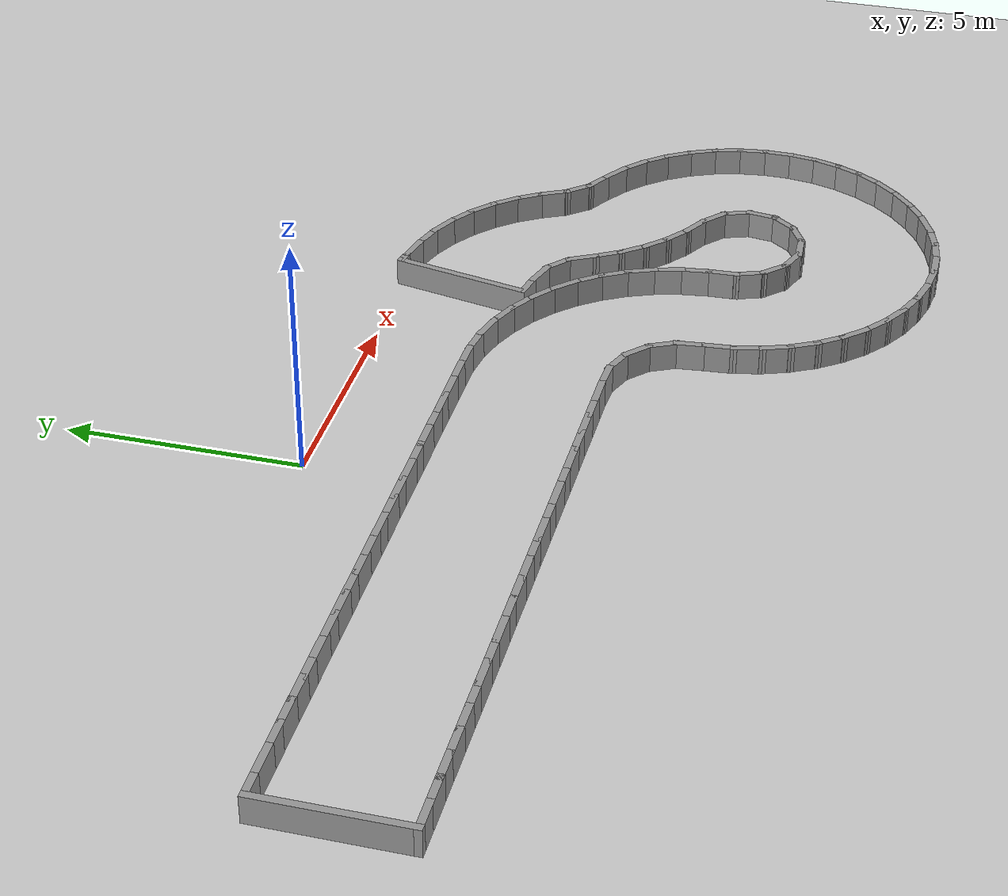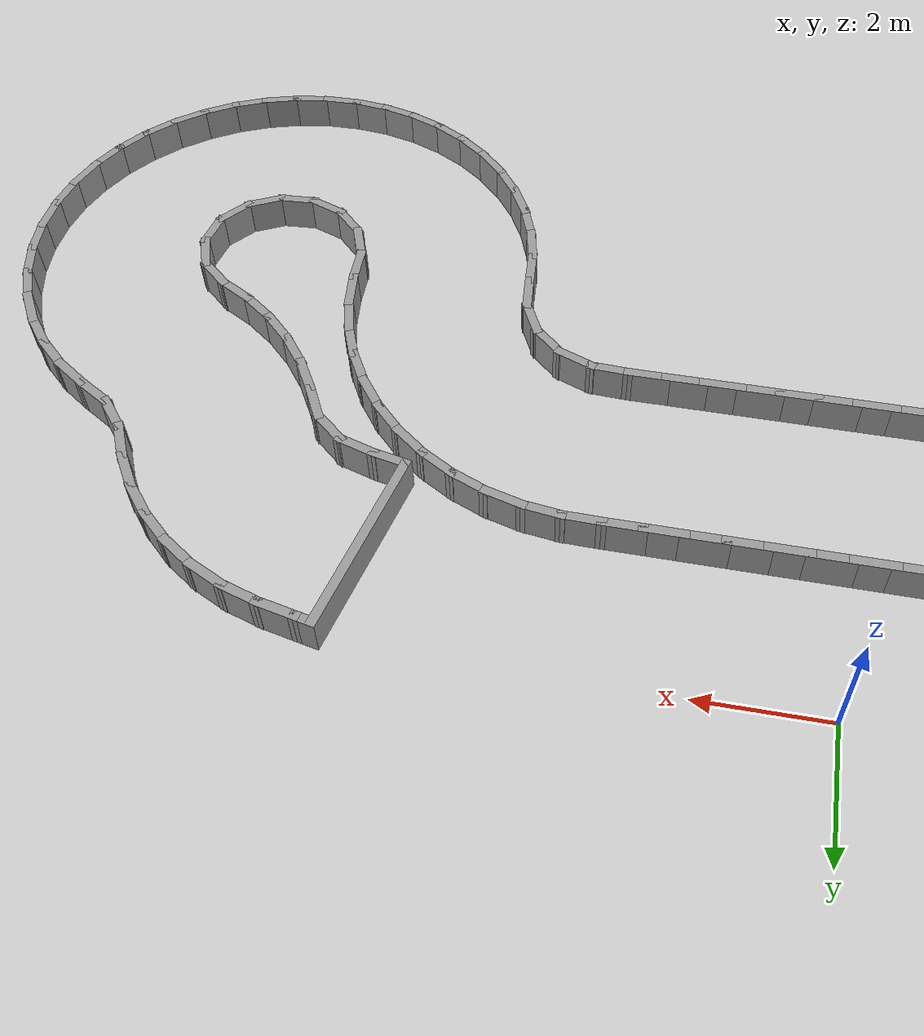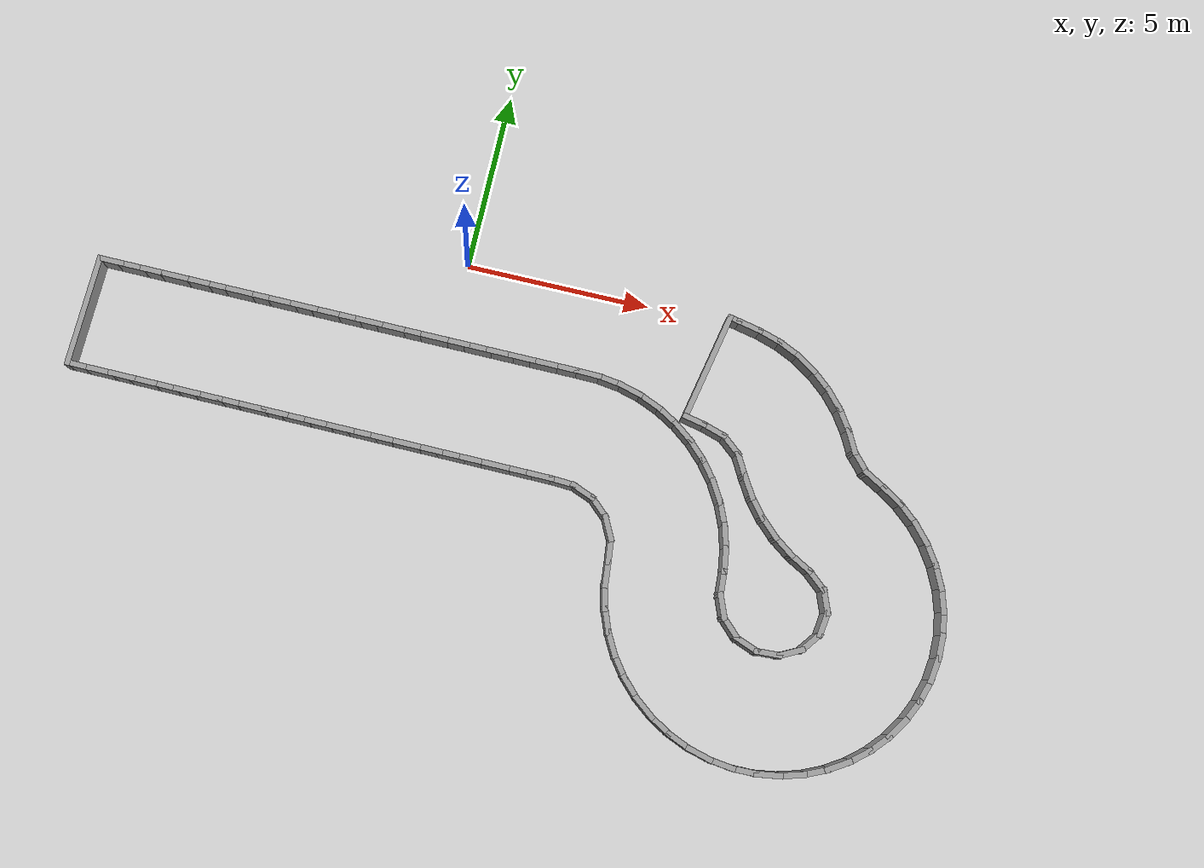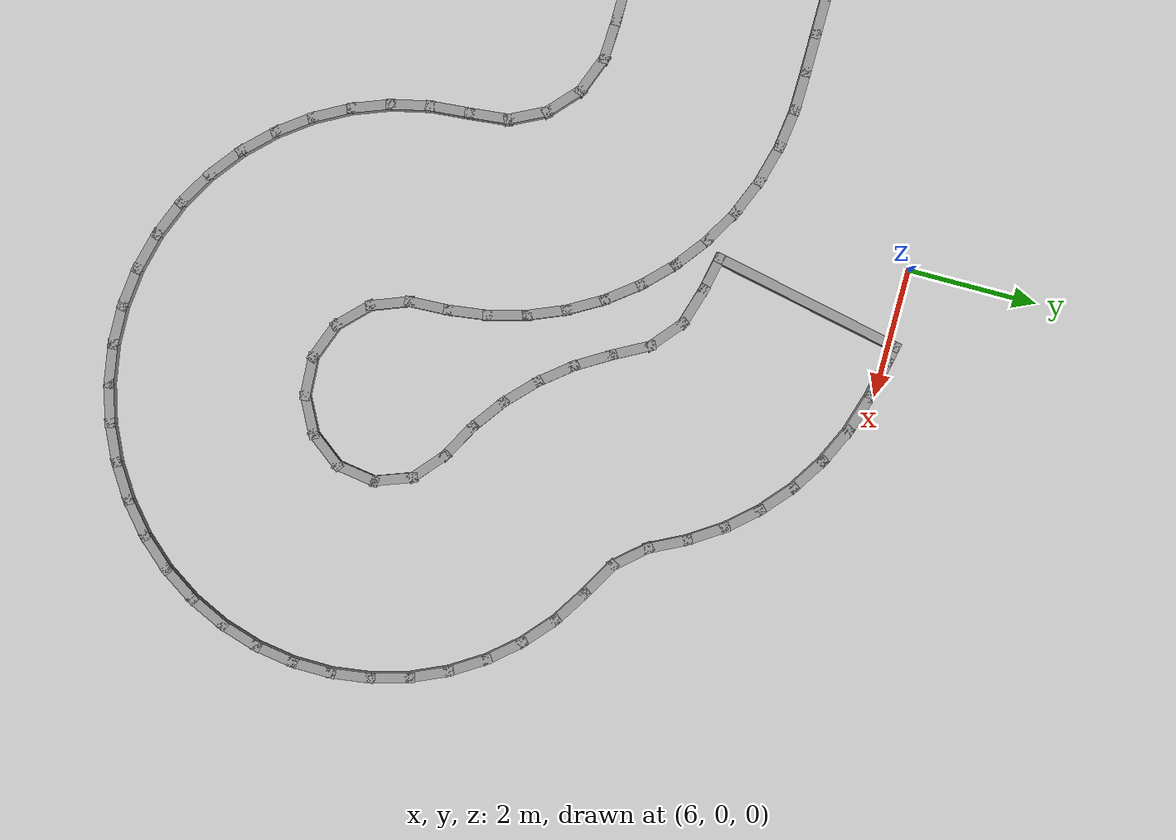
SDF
<?xml version="1.0" ?>
<sdf version='1.7'>
  <world name='default'>
    <plugin name='gazebo_ros_state' filename='libgazebo_ros_state.so'>
      <ros>
        <namespace>/</namespace>
      </ros>
      <update_rate>1000.0</update_rate>
    </plugin>

    <light name='sun' type='directional'>
      <cast_shadows>1</cast_shadows>
      <pose>0 0 10 0 -0 0</pose>
      <diffuse>0.8 0.8 0.8 1</diffuse>
      <specular>0.2 0.2 0.2 1</specular>
      <attenuation>
        <range>1000</range>
        <constant>0.9</constant>
        <linear>0.01</linear>
        <quadratic>0.001</quadratic>
      </attenuation>
      <direction>-0.5 0.1 -0.9</direction>
      <spot>
        <inner_angle>0</inner_angle>
        <outer_angle>0</outer_angle>
        <falloff>0</falloff>
      </spot>
    </light>
    <model name='ground_plane'>
      <static>1</static>
      <link name='link'>
        <collision name='collision'>
          <geometry>
            <plane>
              <normal>0 0 1</normal>
              <size>100 100</size>
            </plane>
          </geometry>
          <surface>
            <friction>
              <ode>
                <mu>100</mu>
                <mu2>50</mu2>
              </ode>
              <torsional>
                <ode/>
              </torsional>
            </friction>
            <contact>
              <ode/>
            </contact>
            <bounce/>
          </surface>
          <max_contacts>10</max_contacts>
        </collision>
        <visual name='visual'>
          <cast_shadows>0</cast_shadows>
          <geometry>
            <plane>
              <normal>0 0 1</normal>
              <size>100 100</size>
            </plane>
          </geometry>
          <material>
            <script>
              <uri>file://media/materials/scripts/gazebo.material</uri>
              <name>Gazebo/Grey</name>
            </script>
          </material>
        </visual>
        <self_collide>0</self_collide>
        <enable_wind>0</enable_wind>
        <kinematic>0</kinematic>
      </link>
    </model>
    <gravity>0 0 -9.8</gravity>
    <magnetic_field>6e-06 2.3e-05 -4.2e-05</magnetic_field>
    <atmosphere type='adiabatic'/>
    <physics type='ode'>
      <max_step_size>0.001</max_step_size>
      <real_time_factor>1</real_time_factor>
      <real_time_update_rate>1000</real_time_update_rate>
    </physics>
    <scene>
      <ambient>0.4 0.4 0.4 1</ambient>
      <background>0.7 0.7 0.7 1</background>
      <shadows>1</shadows>
    </scene>
    <audio>
      <device>default</device>
    </audio>
    <wind/>
    <spherical_coordinates>
      <surface_model>EARTH_WGS84</surface_model>
      <latitude_deg>0</latitude_deg>
      <longitude_deg>0</longitude_deg>
      <elevation>0</elevation>
      <heading_deg>0</heading_deg>
    </spherical_coordinates>
  <model name='rand_turn_13'>
    <pose>0 0 0 0 -0 0</pose>
    <link name='Wall_0'>
      <collision name='Wall_0_Collision'>
        <geometry><box><size>0.7500 0.1500 0.6000</size></box></geometry>
        <pose>0 0 0.3000 0 -0 0</pose>
      </collision>
      <visual name='Wall_0_Visual'>
        <pose>0 0 0.3000 0 -0 0</pose>
        <geometry><box><size>0.7500 0.1500 0.6000</size></box></geometry>
        <material>
          <script>
            <uri>file://media/materials/scripts/gazebo.material</uri>
            <name>Gazebo/Grey</name>
          </script>
          <ambient>1 1 1 1</ambient>
        </material>
      </visual>
      <pose>-9.3673 -2.2573 0 0 -0 -0.00307</pose>
    </link>
    <link name='Wall_1'>
      <collision name='Wall_1_Collision'>
        <geometry><box><size>0.7500 0.1500 0.6000</size></box></geometry>
        <pose>0 0 0.3000 0 -0 0</pose>
      </collision>
      <visual name='Wall_1_Visual'>
        <pose>0 0 0.3000 0 -0 0</pose>
        <geometry><box><size>0.7500 0.1500 0.6000</size></box></geometry>
        <material>
          <script>
            <uri>file://media/materials/scripts/gazebo.material</uri>
            <name>Gazebo/Grey</name>
          </script>
          <ambient>1 1 1 1</ambient>
        </material>
      </visual>
      <pose>-8.7673 -2.2592 0 0 -0 -0.00307</pose>
    </link>
    <link name='Wall_2'>
      <collision name='Wall_2_Collision'>
        <geometry><box><size>0.7500 0.1500 0.6000</size></box></geometry>
        <pose>0 0 0.3000 0 -0 0</pose>
      </collision>
      <visual name='Wall_2_Visual'>
        <pose>0 0 0.3000 0 -0 0</pose>
        <geometry><box><size>0.7500 0.1500 0.6000</size></box></geometry>
        <material>
          <script>
            <uri>file://media/materials/scripts/gazebo.material</uri>
            <name>Gazebo/Grey</name>
          </script>
          <ambient>1 1 1 1</ambient>
        </material>
      </visual>
      <pose>-8.1673 -2.2610 0 0 -0 -0.00307</pose>
    </link>
    <link name='Wall_3'>
      <collision name='Wall_3_Collision'>
        <geometry><box><size>0.7500 0.1500 0.6000</size></box></geometry>
        <pose>0 0 0.3000 0 -0 0</pose>
      </collision>
      <visual name='Wall_3_Visual'>
        <pose>0 0 0.3000 0 -0 0</pose>
        <geometry><box><size>0.7500 0.1500 0.6000</size></box></geometry>
        <material>
          <script>
            <uri>file://media/materials/scripts/gazebo.material</uri>
            <name>Gazebo/Grey</name>
          </script>
          <ambient>1 1 1 1</ambient>
        </material>
      </visual>
      <pose>-7.5673 -2.2629 0 0 -0 -0.00307</pose>
    </link>
    <link name='Wall_4'>
      <collision name='Wall_4_Collision'>
        <geometry><box><size>0.7500 0.1500 0.6000</size></box></geometry>
        <pose>0 0 0.3000 0 -0 0</pose>
      </collision>
      <visual name='Wall_4_Visual'>
        <pose>0 0 0.3000 0 -0 0</pose>
        <geometry><box><size>0.7500 0.1500 0.6000</size></box></geometry>
        <material>
          <script>
            <uri>file://media/materials/scripts/gazebo.material</uri>
            <name>Gazebo/Grey</name>
          </script>
          <ambient>1 1 1 1</ambient>
        </material>
      </visual>
      <pose>-6.9673 -2.2647 0 0 -0 -0.00307</pose>
    </link>
    <link name='Wall_5'>
      <collision name='Wall_5_Collision'>
        <geometry><box><size>0.7500 0.1500 0.6000</size></box></geometry>
        <pose>0 0 0.3000 0 -0 0</pose>
      </collision>
      <visual name='Wall_5_Visual'>
        <pose>0 0 0.3000 0 -0 0</pose>
        <geometry><box><size>0.7500 0.1500 0.6000</size></box></geometry>
        <material>
          <script>
            <uri>file://media/materials/scripts/gazebo.material</uri>
            <name>Gazebo/Grey</name>
          </script>
          <ambient>1 1 1 1</ambient>
        </material>
      </visual>
      <pose>-6.3673 -2.2665 0 0 -0 -0.00307</pose>
    </link>
    <link name='Wall_6'>
      <collision name='Wall_6_Collision'>
        <geometry><box><size>0.7500 0.1500 0.6000</size></box></geometry>
        <pose>0 0 0.3000 0 -0 0</pose>
      </collision>
      <visual name='Wall_6_Visual'>
        <pose>0 0 0.3000 0 -0 0</pose>
        <geometry><box><size>0.7500 0.1500 0.6000</size></box></geometry>
        <material>
          <script>
            <uri>file://media/materials/scripts/gazebo.material</uri>
            <name>Gazebo/Grey</name>
          </script>
          <ambient>1 1 1 1</ambient>
        </material>
      </visual>
      <pose>-5.7674 -2.2684 0 0 -0 -0.00307</pose>
    </link>
    <link name='Wall_7'>
      <collision name='Wall_7_Collision'>
        <geometry><box><size>0.7500 0.1500 0.6000</size></box></geometry>
        <pose>0 0 0.3000 0 -0 0</pose>
      </collision>
      <visual name='Wall_7_Visual'>
        <pose>0 0 0.3000 0 -0 0</pose>
        <geometry><box><size>0.7500 0.1500 0.6000</size></box></geometry>
        <material>
          <script>
            <uri>file://media/materials/scripts/gazebo.material</uri>
            <name>Gazebo/Grey</name>
          </script>
          <ambient>1 1 1 1</ambient>
        </material>
      </visual>
      <pose>-5.1674 -2.2702 0 0 -0 -0.00307</pose>
    </link>
    <link name='Wall_8'>
      <collision name='Wall_8_Collision'>
        <geometry><box><size>0.7500 0.1500 0.6000</size></box></geometry>
        <pose>0 0 0.3000 0 -0 0</pose>
      </collision>
      <visual name='Wall_8_Visual'>
        <pose>0 0 0.3000 0 -0 0</pose>
        <geometry><box><size>0.7500 0.1500 0.6000</size></box></geometry>
        <material>
          <script>
            <uri>file://media/materials/scripts/gazebo.material</uri>
            <name>Gazebo/Grey</name>
          </script>
          <ambient>1 1 1 1</ambient>
        </material>
      </visual>
      <pose>-4.5674 -2.2721 0 0 -0 -0.00307</pose>
    </link>
    <link name='Wall_9'>
      <collision name='Wall_9_Collision'>
        <geometry><box><size>0.7500 0.1500 0.6000</size></box></geometry>
        <pose>0 0 0.3000 0 -0 0</pose>
      </collision>
      <visual name='Wall_9_Visual'>
        <pose>0 0 0.3000 0 -0 0</pose>
        <geometry><box><size>0.7500 0.1500 0.6000</size></box></geometry>
        <material>
          <script>
            <uri>file://media/materials/scripts/gazebo.material</uri>
            <name>Gazebo/Grey</name>
          </script>
          <ambient>1 1 1 1</ambient>
        </material>
      </visual>
      <pose>-3.9674 -2.2739 0 0 -0 -0.00307</pose>
    </link>
    <link name='Wall_10'>
      <collision name='Wall_10_Collision'>
        <geometry><box><size>0.7500 0.1500 0.6000</size></box></geometry>
        <pose>0 0 0.3000 0 -0 0</pose>
      </collision>
      <visual name='Wall_10_Visual'>
        <pose>0 0 0.3000 0 -0 0</pose>
        <geometry><box><size>0.7500 0.1500 0.6000</size></box></geometry>
        <material>
          <script>
            <uri>file://media/materials/scripts/gazebo.material</uri>
            <name>Gazebo/Grey</name>
          </script>
          <ambient>1 1 1 1</ambient>
        </material>
      </visual>
      <pose>-3.3674 -2.2758 0 0 -0 -0.00307</pose>
    </link>
    <link name='Wall_11'>
      <collision name='Wall_11_Collision'>
        <geometry><box><size>0.7500 0.1500 0.6000</size></box></geometry>
        <pose>0 0 0.3000 0 -0 0</pose>
      </collision>
      <visual name='Wall_11_Visual'>
        <pose>0 0 0.3000 0 -0 0</pose>
        <geometry><box><size>0.7500 0.1500 0.6000</size></box></geometry>
        <material>
          <script>
            <uri>file://media/materials/scripts/gazebo.material</uri>
            <name>Gazebo/Grey</name>
          </script>
          <ambient>1 1 1 1</ambient>
        </material>
      </visual>
      <pose>-2.7674 -2.2776 0 0 -0 -0.00307</pose>
    </link>
    <link name='Wall_12'>
      <collision name='Wall_12_Collision'>
        <geometry><box><size>0.7500 0.1500 0.6000</size></box></geometry>
        <pose>0 0 0.3000 0 -0 0</pose>
      </collision>
      <visual name='Wall_12_Visual'>
        <pose>0 0 0.3000 0 -0 0</pose>
        <geometry><box><size>0.7500 0.1500 0.6000</size></box></geometry>
        <material>
          <script>
            <uri>file://media/materials/scripts/gazebo.material</uri>
            <name>Gazebo/Grey</name>
          </script>
          <ambient>1 1 1 1</ambient>
        </material>
      </visual>
      <pose>-2.1674 -2.2794 0 0 -0 -0.00307</pose>
    </link>
    <link name='Wall_13'>
      <collision name='Wall_13_Collision'>
        <geometry><box><size>0.7500 0.1500 0.6000</size></box></geometry>
        <pose>0 0 0.3000 0 -0 0</pose>
      </collision>
      <visual name='Wall_13_Visual'>
        <pose>0 0 0.3000 0 -0 0</pose>
        <geometry><box><size>0.7500 0.1500 0.6000</size></box></geometry>
        <material>
          <script>
            <uri>file://media/materials/scripts/gazebo.material</uri>
            <name>Gazebo/Grey</name>
          </script>
          <ambient>1 1 1 1</ambient>
        </material>
      </visual>
      <pose>-1.5674 -2.2813 0 0 -0 -0.00307</pose>
    </link>
    <link name='Wall_14'>
      <collision name='Wall_14_Collision'>
        <geometry><box><size>0.7500 0.1500 0.6000</size></box></geometry>
        <pose>0 0 0.3000 0 -0 0</pose>
      </collision>
      <visual name='Wall_14_Visual'>
        <pose>0 0 0.3000 0 -0 0</pose>
        <geometry><box><size>0.7500 0.1500 0.6000</size></box></geometry>
        <material>
          <script>
            <uri>file://media/materials/scripts/gazebo.material</uri>
            <name>Gazebo/Grey</name>
          </script>
          <ambient>1 1 1 1</ambient>
        </material>
      </visual>
      <pose>-0.9674 -2.2831 0 0 -0 -0.00307</pose>
    </link>
    <link name='Wall_15'>
      <collision name='Wall_15_Collision'>
        <geometry><box><size>0.7500 0.1500 0.6000</size></box></geometry>
        <pose>0 0 0.3000 0 -0 0</pose>
      </collision>
      <visual name='Wall_15_Visual'>
        <pose>0 0 0.3000 0 -0 0</pose>
        <geometry><box><size>0.7500 0.1500 0.6000</size></box></geometry>
        <material>
          <script>
            <uri>file://media/materials/scripts/gazebo.material</uri>
            <name>Gazebo/Grey</name>
          </script>
          <ambient>1 1 1 1</ambient>
        </material>
      </visual>
      <pose>-0.3674 -2.2850 0 0 -0 -0.00307</pose>
    </link>
    <link name='Wall_16'>
      <collision name='Wall_16_Collision'>
        <geometry><box><size>0.7500 0.1500 0.6000</size></box></geometry>
        <pose>0 0 0.3000 0 -0 0</pose>
      </collision>
      <visual name='Wall_16_Visual'>
        <pose>0 0 0.3000 0 -0 0</pose>
        <geometry><box><size>0.7500 0.1500 0.6000</size></box></geometry>
        <material>
          <script>
            <uri>file://media/materials/scripts/gazebo.material</uri>
            <name>Gazebo/Grey</name>
          </script>
          <ambient>1 1 1 1</ambient>
        </material>
      </visual>
      <pose>0.2326 -2.2868 0 0 -0 -0.00307</pose>
    </link>
    <link name='Wall_17'>
      <collision name='Wall_17_Collision'>
        <geometry><box><size>0.7500 0.1500 0.6000</size></box></geometry>
        <pose>0 0 0.3000 0 -0 0</pose>
      </collision>
      <visual name='Wall_17_Visual'>
        <pose>0 0 0.3000 0 -0 0</pose>
        <geometry><box><size>0.7500 0.1500 0.6000</size></box></geometry>
        <material>
          <script>
            <uri>file://media/materials/scripts/gazebo.material</uri>
            <name>Gazebo/Grey</name>
          </script>
          <ambient>1 1 1 1</ambient>
        </material>
      </visual>
      <pose>0.8326 -2.2887 0 0 -0 -0.00307</pose>
    </link>
    <link name='Wall_18'>
      <collision name='Wall_18_Collision'>
        <geometry><box><size>0.7500 0.1500 0.6000</size></box></geometry>
        <pose>0 0 0.3000 0 -0 0</pose>
      </collision>
      <visual name='Wall_18_Visual'>
        <pose>0 0 0.3000 0 -0 0</pose>
        <geometry><box><size>0.7500 0.1500 0.6000</size></box></geometry>
        <material>
          <script>
            <uri>file://media/materials/scripts/gazebo.material</uri>
            <name>Gazebo/Grey</name>
          </script>
          <ambient>1 1 1 1</ambient>
        </material>
      </visual>
      <pose>1.4326 -2.2905 0 0 -0 -0.00307</pose>
    </link>
    <link name='Wall_19'>
      <collision name='Wall_19_Collision'>
        <geometry><box><size>0.7500 0.1500 0.6000</size></box></geometry>
        <pose>0 0 0.3000 0 -0 0</pose>
      </collision>
      <visual name='Wall_19_Visual'>
        <pose>0 0 0.3000 0 -0 0</pose>
        <geometry><box><size>0.7500 0.1500 0.6000</size></box></geometry>
        <material>
          <script>
            <uri>file://media/materials/scripts/gazebo.material</uri>
            <name>Gazebo/Grey</name>
          </script>
          <ambient>1 1 1 1</ambient>
        </material>
      </visual>
      <pose>2.0326 -2.2923 0 0 -0 -0.00307</pose>
    </link>
    <link name='Wall_20'>
      <collision name='Wall_20_Collision'>
        <geometry><box><size>0.7500 0.1500 0.6000</size></box></geometry>
        <pose>0 0 0.3000 0 -0 0</pose>
      </collision>
      <visual name='Wall_20_Visual'>
        <pose>0 0 0.3000 0 -0 0</pose>
        <geometry><box><size>0.7500 0.1500 0.6000</size></box></geometry>
        <material>
          <script>
            <uri>file://media/materials/scripts/gazebo.material</uri>
            <name>Gazebo/Grey</name>
          </script>
          <ambient>1 1 1 1</ambient>
        </material>
      </visual>
      <pose>2.6326 -2.2942 0 0 -0 -0.00307</pose>
    </link>
    <link name='Wall_21'>
      <collision name='Wall_21_Collision'>
        <geometry><box><size>0.7500 0.1500 0.6000</size></box></geometry>
        <pose>0 0 0.3000 0 -0 0</pose>
      </collision>
      <visual name='Wall_21_Visual'>
        <pose>0 0 0.3000 0 -0 0</pose>
        <geometry><box><size>0.7500 0.1500 0.6000</size></box></geometry>
        <material>
          <script>
            <uri>file://media/materials/scripts/gazebo.material</uri>
            <name>Gazebo/Grey</name>
          </script>
          <ambient>1 1 1 1</ambient>
        </material>
      </visual>
      <pose>3.2326 -2.2960 0 0 -0 -0.00307</pose>
    </link>
    <link name='Wall_22'>
      <collision name='Wall_22_Collision'>
        <geometry><box><size>0.7499 0.1500 0.6000</size></box></geometry>
        <pose>0 0 0.3000 0 -0 0</pose>
      </collision>
      <visual name='Wall_22_Visual'>
        <pose>0 0 0.3000 0 -0 0</pose>
        <geometry><box><size>0.7499 0.1500 0.6000</size></box></geometry>
        <material>
          <script>
            <uri>file://media/materials/scripts/gazebo.material</uri>
            <name>Gazebo/Grey</name>
          </script>
          <ambient>1 1 1 1</ambient>
        </material>
      </visual>
      <pose>3.8325 -2.3028 0 0 -0 -0.01951</pose>
    </link>
    <link name='Wall_23'>
      <collision name='Wall_23_Collision'>
        <geometry><box><size>0.7496 0.1500 0.6000</size></box></geometry>
        <pose>0 0 0.3000 0 -0 0</pose>
      </collision>
      <visual name='Wall_23_Visual'>
        <pose>0 0 0.3000 0 -0 0</pose>
        <geometry><box><size>0.7496 0.1500 0.6000</size></box></geometry>
        <material>
          <script>
            <uri>file://media/materials/scripts/gazebo.material</uri>
            <name>Gazebo/Grey</name>
          </script>
          <ambient>1 1 1 1</ambient>
        </material>
      </visual>
      <pose>4.4295 -2.3487 0 0 -0 -0.13390</pose>
    </link>
    <link name='Wall_24'>
      <collision name='Wall_24_Collision'>
        <geometry><box><size>0.7496 0.1500 0.6000</size></box></geometry>
        <pose>0 0 0.3000 0 -0 0</pose>
      </collision>
      <visual name='Wall_24_Visual'>
        <pose>0 0 0.3000 0 -0 0</pose>
        <geometry><box><size>0.7496 0.1500 0.6000</size></box></geometry>
        <material>
          <script>
            <uri>file://media/materials/scripts/gazebo.material</uri>
            <name>Gazebo/Grey</name>
          </script>
          <ambient>1 1 1 1</ambient>
        </material>
      </visual>
      <pose>5.0159 -2.4671 0 0 -0 -0.26449</pose>
    </link>
    <link name='Wall_25'>
      <collision name='Wall_25_Collision'>
        <geometry><box><size>0.7496 0.1500 0.6000</size></box></geometry>
        <pose>0 0 0.3000 0 -0 0</pose>
      </collision>
      <visual name='Wall_25_Visual'>
        <pose>0 0 0.3000 0 -0 0</pose>
        <geometry><box><size>0.7496 0.1500 0.6000</size></box></geometry>
        <material>
          <script>
            <uri>file://media/materials/scripts/gazebo.material</uri>
            <name>Gazebo/Grey</name>
          </script>
          <ambient>1 1 1 1</ambient>
        </material>
      </visual>
      <pose>5.5820 -2.6608 0 0 -0 -0.39508</pose>
    </link>
    <link name='Wall_26'>
      <collision name='Wall_26_Collision'>
        <geometry><box><size>0.7495 0.1500 0.6000</size></box></geometry>
        <pose>0 0 0.3000 0 -0 0</pose>
      </collision>
      <visual name='Wall_26_Visual'>
        <pose>0 0 0.3000 0 -0 0</pose>
        <geometry><box><size>0.7495 0.1500 0.6000</size></box></geometry>
        <material>
          <script>
            <uri>file://media/materials/scripts/gazebo.material</uri>
            <name>Gazebo/Grey</name>
          </script>
          <ambient>1 1 1 1</ambient>
        </material>
      </visual>
      <pose>6.1180 -2.9266 0 0 -0 -0.52568</pose>
    </link>
    <link name='Wall_27'>
      <collision name='Wall_27_Collision'>
        <geometry><box><size>0.7495 0.1500 0.6000</size></box></geometry>
        <pose>0 0 0.3000 0 -0 0</pose>
      </collision>
      <visual name='Wall_27_Visual'>
        <pose>0 0 0.3000 0 -0 0</pose>
        <geometry><box><size>0.7495 0.1500 0.6000</size></box></geometry>
        <material>
          <script>
            <uri>file://media/materials/scripts/gazebo.material</uri>
            <name>Gazebo/Grey</name>
          </script>
          <ambient>1 1 1 1</ambient>
        </material>
      </visual>
      <pose>6.6148 -3.2600 0 0 -0 -0.65627</pose>
    </link>
    <link name='Wall_28'>
      <collision name='Wall_28_Collision'>
        <geometry><box><size>0.7495 0.1500 0.6000</size></box></geometry>
        <pose>0 0 0.3000 0 -0 0</pose>
      </collision>
      <visual name='Wall_28_Visual'>
        <pose>0 0 0.3000 0 -0 0</pose>
        <geometry><box><size>0.7495 0.1500 0.6000</size></box></geometry>
        <material>
          <script>
            <uri>file://media/materials/scripts/gazebo.material</uri>
            <name>Gazebo/Grey</name>
          </script>
          <ambient>1 1 1 1</ambient>
        </material>
      </visual>
      <pose>7.0639 -3.6551 0 0 -0 -0.78686</pose>
    </link>
    <link name='Wall_29'>
      <collision name='Wall_29_Collision'>
        <geometry><box><size>0.7495 0.1500 0.6000</size></box></geometry>
        <pose>0 0 0.3000 0 -0 0</pose>
      </collision>
      <visual name='Wall_29_Visual'>
        <pose>0 0 0.3000 0 -0 0</pose>
        <geometry><box><size>0.7495 0.1500 0.6000</size></box></geometry>
        <material>
          <script>
            <uri>file://media/materials/scripts/gazebo.material</uri>
            <name>Gazebo/Grey</name>
          </script>
          <ambient>1 1 1 1</ambient>
        </material>
      </visual>
      <pose>7.4578 -4.1054 0 0 -0 -0.91745</pose>
    </link>
    <link name='Wall_30'>
      <collision name='Wall_30_Collision'>
        <geometry><box><size>0.7495 0.1500 0.6000</size></box></geometry>
        <pose>0 0 0.3000 0 -0 0</pose>
      </collision>
      <visual name='Wall_30_Visual'>
        <pose>0 0 0.3000 0 -0 0</pose>
        <geometry><box><size>0.7495 0.1500 0.6000</size></box></geometry>
        <material>
          <script>
            <uri>file://media/materials/scripts/gazebo.material</uri>
            <name>Gazebo/Grey</name>
          </script>
          <ambient>1 1 1 1</ambient>
        </material>
      </visual>
      <pose>7.7896 -4.6032 0 0 -0 -1.04805</pose>
    </link>
    <link name='Wall_31'>
      <collision name='Wall_31_Collision'>
        <geometry><box><size>0.7495 0.1500 0.6000</size></box></geometry>
        <pose>0 0 0.3000 0 -0 0</pose>
      </collision>
      <visual name='Wall_31_Visual'>
        <pose>0 0 0.3000 0 -0 0</pose>
        <geometry><box><size>0.7495 0.1500 0.6000</size></box></geometry>
        <material>
          <script>
            <uri>file://media/materials/scripts/gazebo.material</uri>
            <name>Gazebo/Grey</name>
          </script>
          <ambient>1 1 1 1</ambient>
        </material>
      </visual>
      <pose>8.0539 -5.1399 0 0 -0 -1.17864</pose>
    </link>
    <link name='Wall_32'>
      <collision name='Wall_32_Collision'>
        <geometry><box><size>0.7495 0.1500 0.6000</size></box></geometry>
        <pose>0 0 0.3000 0 -0 0</pose>
      </collision>
      <visual name='Wall_32_Visual'>
        <pose>0 0 0.3000 0 -0 0</pose>
        <geometry><box><size>0.7495 0.1500 0.6000</size></box></geometry>
        <material>
          <script>
            <uri>file://media/materials/scripts/gazebo.material</uri>
            <name>Gazebo/Grey</name>
          </script>
          <ambient>1 1 1 1</ambient>
        </material>
      </visual>
      <pose>8.2459 -5.7065 0 0 -0 -1.30923</pose>
    </link>
    <link name='Wall_33'>
      <collision name='Wall_33_Collision'>
        <geometry><box><size>0.7495 0.1500 0.6000</size></box></geometry>
        <pose>0 0 0.3000 0 -0 0</pose>
      </collision>
      <visual name='Wall_33_Visual'>
        <pose>0 0 0.3000 0 -0 0</pose>
        <geometry><box><size>0.7495 0.1500 0.6000</size></box></geometry>
        <material>
          <script>
            <uri>file://media/materials/scripts/gazebo.material</uri>
            <name>Gazebo/Grey</name>
          </script>
          <ambient>1 1 1 1</ambient>
        </material>
      </visual>
      <pose>8.3626 -6.2933 0 0 -0 -1.43982</pose>
    </link>
    <link name='Wall_34'>
      <collision name='Wall_34_Collision'>
        <geometry><box><size>0.7495 0.1500 0.6000</size></box></geometry>
        <pose>0 0 0.3000 0 -0 0</pose>
      </collision>
      <visual name='Wall_34_Visual'>
        <pose>0 0 0.3000 0 -0 0</pose>
        <geometry><box><size>0.7495 0.1500 0.6000</size></box></geometry>
        <material>
          <script>
            <uri>file://media/materials/scripts/gazebo.material</uri>
            <name>Gazebo/Grey</name>
          </script>
          <ambient>1 1 1 1</ambient>
        </material>
      </visual>
      <pose>8.4148 -6.8899 0 0 -0 -1.52728</pose>
    </link>
    <link name='Wall_35'>
      <collision name='Wall_35_Collision'>
        <geometry><box><size>0.7456 0.1500 0.6000</size></box></geometry>
        <pose>0 0 0.3000 0 -0 0</pose>
      </collision>
      <visual name='Wall_35_Visual'>
        <pose>0 0 0.3000 0 -0 0</pose>
        <geometry><box><size>0.7456 0.1500 0.6000</size></box></geometry>
        <material>
          <script>
            <uri>file://media/materials/scripts/gazebo.material</uri>
            <name>Gazebo/Grey</name>
          </script>
          <ambient>1 1 1 1</ambient>
        </material>
      </visual>
      <pose>8.5335 -7.4678 0 0 -0 -1.20817</pose>
    </link>
    <link name='Wall_36'>
      <collision name='Wall_36_Collision'>
        <geometry><box><size>0.7455 0.1500 0.6000</size></box></geometry>
        <pose>0 0 0.3000 0 -0 0</pose>
      </collision>
      <visual name='Wall_36_Visual'>
        <pose>0 0 0.3000 0 -0 0</pose>
        <geometry><box><size>0.7455 0.1500 0.6000</size></box></geometry>
        <material>
          <script>
            <uri>file://media/materials/scripts/gazebo.material</uri>
            <name>Gazebo/Grey</name>
          </script>
          <ambient>1 1 1 1</ambient>
        </material>
      </visual>
      <pose>8.8494 -7.9570 0 0 -0 -0.78662</pose>
    </link>
    <link name='Wall_37'>
      <collision name='Wall_37_Collision'>
        <geometry><box><size>0.7455 0.1500 0.6000</size></box></geometry>
        <pose>0 0 0.3000 0 -0 0</pose>
      </collision>
      <visual name='Wall_37_Visual'>
        <pose>0 0 0.3000 0 -0 0</pose>
        <geometry><box><size>0.7455 0.1500 0.6000</size></box></geometry>
        <material>
          <script>
            <uri>file://media/materials/scripts/gazebo.material</uri>
            <name>Gazebo/Grey</name>
          </script>
          <ambient>1 1 1 1</ambient>
        </material>
      </visual>
      <pose>9.3378 -8.2742 0 0 -0 -0.36515</pose>
    </link>
    <link name='Wall_38'>
      <collision name='Wall_38_Collision'>
        <geometry><box><size>0.7455 0.1500 0.6000</size></box></geometry>
        <pose>0 0 0.3000 0 -0 0</pose>
      </collision>
      <visual name='Wall_38_Visual'>
        <pose>0 0 0.3000 0 -0 0</pose>
        <geometry><box><size>0.7455 0.1500 0.6000</size></box></geometry>
        <material>
          <script>
            <uri>file://media/materials/scripts/gazebo.material</uri>
            <name>Gazebo/Grey</name>
          </script>
          <ambient>1 1 1 1</ambient>
        </material>
      </visual>
      <pose>9.9132 -8.3627 0 0 -0 0.05997</pose>
    </link>
    <link name='Wall_39'>
      <collision name='Wall_39_Collision'>
        <geometry><box><size>0.7458 0.1500 0.6000</size></box></geometry>
        <pose>0 0 0.3000 0 -0 0</pose>
      </collision>
      <visual name='Wall_39_Visual'>
        <pose>0 0 0.3000 0 -0 0</pose>
        <geometry><box><size>0.7458 0.1500 0.6000</size></box></geometry>
        <material>
          <script>
            <uri>file://media/materials/scripts/gazebo.material</uri>
            <name>Gazebo/Grey</name>
          </script>
          <ambient>1 1 1 1</ambient>
        </material>
      </visual>
      <pose>10.4753 -8.2085 0 0 -0 0.47515</pose>
    </link>
    <link name='Wall_40'>
      <collision name='Wall_40_Collision'>
        <geometry><box><size>0.7437 0.1500 0.6000</size></box></geometry>
        <pose>0 0 0.3000 0 -0 0</pose>
      </collision>
      <visual name='Wall_40_Visual'>
        <pose>0 0 0.3000 0 -0 0</pose>
        <geometry><box><size>0.7437 0.1500 0.6000</size></box></geometry>
        <material>
          <script>
            <uri>file://media/materials/scripts/gazebo.material</uri>
            <name>Gazebo/Grey</name>
          </script>
          <ambient>1 1 1 1</ambient>
        </material>
      </visual>
      <pose>10.9215 -7.8373 0 0 -0 0.91355</pose>
    </link>
    <link name='Wall_41'>
      <collision name='Wall_41_Collision'>
        <geometry><box><size>0.7436 0.1500 0.6000</size></box></geometry>
        <pose>0 0 0.3000 0 -0 0</pose>
      </collision>
      <visual name='Wall_41_Visual'>
        <pose>0 0 0.3000 0 -0 0</pose>
        <geometry><box><size>0.7436 0.1500 0.6000</size></box></geometry>
        <material>
          <script>
            <uri>file://media/materials/scripts/gazebo.material</uri>
            <name>Gazebo/Grey</name>
          </script>
          <ambient>1 1 1 1</ambient>
        </material>
      </visual>
      <pose>11.1479 -7.3089 0 0 -0 1.41856</pose>
    </link>
    <link name='Wall_42'>
      <collision name='Wall_42_Collision'>
        <geometry><box><size>0.7436 0.1500 0.6000</size></box></geometry>
        <pose>0 0 0.3000 0 -0 0</pose>
      </collision>
      <visual name='Wall_42_Visual'>
        <pose>0 0 0.3000 0 -0 0</pose>
        <geometry><box><size>0.7436 0.1500 0.6000</size></box></geometry>
        <material>
          <script>
            <uri>file://media/materials/scripts/gazebo.material</uri>
            <name>Gazebo/Grey</name>
          </script>
          <ambient>1 1 1 1</ambient>
        </material>
      </visual>
      <pose>11.0906 -6.7368 0 0 -0 1.92269</pose>
    </link>
    <link name='Wall_43'>
      <collision name='Wall_43_Collision'>
        <geometry><box><size>0.7436 0.1500 0.6000</size></box></geometry>
        <pose>0 0 0.3000 0 -0 0</pose>
      </collision>
      <visual name='Wall_43_Visual'>
        <pose>0 0 0.3000 0 -0 0</pose>
        <geometry><box><size>0.7436 0.1500 0.6000</size></box></geometry>
        <material>
          <script>
            <uri>file://media/materials/scripts/gazebo.material</uri>
            <name>Gazebo/Grey</name>
          </script>
          <ambient>1 1 1 1</ambient>
        </material>
      </visual>
      <pose>10.7642 -6.2636 0 0 -0 2.42638</pose>
    </link>
    <link name='Wall_44'>
      <collision name='Wall_44_Collision'>
        <geometry><box><size>0.7496 0.1500 0.6000</size></box></geometry>
        <pose>0 0 0.3000 0 -0 0</pose>
      </collision>
      <visual name='Wall_44_Visual'>
        <pose>0 0 0.3000 0 -0 0</pose>
        <geometry><box><size>0.7496 0.1500 0.6000</size></box></geometry>
        <material>
          <script>
            <uri>file://media/materials/scripts/gazebo.material</uri>
            <name>Gazebo/Grey</name>
          </script>
          <ambient>1 1 1 1</ambient>
        </material>
      </visual>
      <pose>10.2779 -5.9237 0 0 -0 2.63589</pose>
    </link>
    <link name='Wall_45'>
      <collision name='Wall_45_Collision'>
        <geometry><box><size>0.7495 0.1500 0.6000</size></box></geometry>
        <pose>0 0 0.3000 0 -0 0</pose>
      </collision>
      <visual name='Wall_45_Visual'>
        <pose>0 0 0.3000 0 -0 0</pose>
        <geometry><box><size>0.7495 0.1500 0.6000</size></box></geometry>
        <material>
          <script>
            <uri>file://media/materials/scripts/gazebo.material</uri>
            <name>Gazebo/Grey</name>
          </script>
          <ambient>1 1 1 1</ambient>
        </material>
      </visual>
      <pose>9.7745 -5.6004 0 0 -0 2.50560</pose>
    </link>
    <link name='Wall_46'>
      <collision name='Wall_46_Collision'>
        <geometry><box><size>0.7495 0.1500 0.6000</size></box></geometry>
        <pose>0 0 0.3000 0 -0 0</pose>
      </collision>
      <visual name='Wall_46_Visual'>
        <pose>0 0 0.3000 0 -0 0</pose>
        <geometry><box><size>0.7495 0.1500 0.6000</size></box></geometry>
        <material>
          <script>
            <uri>file://media/materials/scripts/gazebo.material</uri>
            <name>Gazebo/Grey</name>
          </script>
          <ambient>1 1 1 1</ambient>
        </material>
      </visual>
      <pose>9.3175 -5.2144 0 0 -0 2.37460</pose>
    </link>
    <link name='Wall_47'>
      <collision name='Wall_47_Collision'>
        <geometry><box><size>0.7495 0.1500 0.6000</size></box></geometry>
        <pose>0 0 0.3000 0 -0 0</pose>
      </collision>
      <visual name='Wall_47_Visual'>
        <pose>0 0 0.3000 0 -0 0</pose>
        <geometry><box><size>0.7495 0.1500 0.6000</size></box></geometry>
        <material>
          <script>
            <uri>file://media/materials/scripts/gazebo.material</uri>
            <name>Gazebo/Grey</name>
          </script>
          <ambient>1 1 1 1</ambient>
        </material>
      </visual>
      <pose>8.9148 -4.7719 0 0 -0 2.24360</pose>
    </link>
    <link name='Wall_48'>
      <collision name='Wall_48_Collision'>
        <geometry><box><size>0.7495 0.1500 0.6000</size></box></geometry>
        <pose>0 0 0.3000 0 -0 0</pose>
      </collision>
      <visual name='Wall_48_Visual'>
        <pose>0 0 0.3000 0 -0 0</pose>
        <geometry><box><size>0.7495 0.1500 0.6000</size></box></geometry>
        <material>
          <script>
            <uri>file://media/materials/scripts/gazebo.material</uri>
            <name>Gazebo/Grey</name>
          </script>
          <ambient>1 1 1 1</ambient>
        </material>
      </visual>
      <pose>8.5735 -4.2806 0 0 -0 2.11259</pose>
    </link>
    <link name='Wall_49'>
      <collision name='Wall_49_Collision'>
        <geometry><box><size>0.7487 0.1500 0.6000</size></box></geometry>
        <pose>0 0 0.3000 0 -0 0</pose>
      </collision>
      <visual name='Wall_49_Visual'>
        <pose>0 0 0.3000 0 -0 0</pose>
        <geometry><box><size>0.7487 0.1500 0.6000</size></box></geometry>
        <material>
          <script>
            <uri>file://media/materials/scripts/gazebo.material</uri>
            <name>Gazebo/Grey</name>
          </script>
          <ambient>1 1 1 1</ambient>
        </material>
      </visual>
      <pose>8.2774 -3.7600 0 0 -0 2.06303</pose>
    </link>
    <link name='Wall_50'>
      <collision name='Wall_50_Collision'>
        <geometry><box><size>0.7452 0.1500 0.6000</size></box></geometry>
        <pose>0 0 0.3000 0 -0 0</pose>
      </collision>
      <visual name='Wall_50_Visual'>
        <pose>0 0 0.3000 0 -0 0</pose>
        <geometry><box><size>0.7452 0.1500 0.6000</size></box></geometry>
        <material>
          <script>
            <uri>file://media/materials/scripts/gazebo.material</uri>
            <name>Gazebo/Grey</name>
          </script>
          <ambient>1 1 1 1</ambient>
        </material>
      </visual>
      <pose>7.9091 -3.3036 0 0 -0 2.43771</pose>
    </link>
    <link name='Wall_51'>
      <collision name='Wall_51_Collision'>
        <geometry><box><size>0.7473 0.1500 0.6000</size></box></geometry>
        <pose>0 0 0.3000 0 -0 0</pose>
      </collision>
      <visual name='Wall_51_Visual'>
        <pose>0 0 0.3000 0 -0 0</pose>
        <geometry><box><size>0.7473 0.1500 0.6000</size></box></geometry>
        <material>
          <script>
            <uri>file://media/materials/scripts/gazebo.material</uri>
            <name>Gazebo/Grey</name>
          </script>
          <ambient>1 1 1 1</ambient>
        </material>
      </visual>
      <pose>7.3965 -3.0239 0 0 -0 2.84577</pose>
    </link>
    <link name='Wall_52'>
      <collision name='Wall_52_Collision'>
        <geometry><box><size>0.6847 0.1500 0.6000</size></box></geometry>
        <pose>0 0 0.3000 0 -0 0</pose>
      </collision>
      <visual name='Wall_52_Visual'>
        <pose>0 0 0.3000 0 -0 0</pose>
        <geometry><box><size>0.6847 0.1500 0.6000</size></box></geometry>
        <material>
          <script>
            <uri>file://media/materials/scripts/gazebo.material</uri>
            <name>Gazebo/Grey</name>
          </script>
          <ambient>1 1 1 1</ambient>
        </material>
      </visual>
      <pose>6.8491 -2.8820 0 0 -0 2.93494</pose>
    </link>
    <link name='Wall_53'>
      <collision name='Wall_53_Collision'>
        <geometry><box><size>0.7500 0.1500 0.6000</size></box></geometry>
        <pose>0 0 0.3000 0 -0 0</pose>
      </collision>
      <visual name='Wall_53_Visual'>
        <pose>0 0 0.3000 0 -0 0</pose>
        <geometry><box><size>0.7500 0.1500 0.6000</size></box></geometry>
        <material>
          <script>
            <uri>file://media/materials/scripts/gazebo.material</uri>
            <name>Gazebo/Grey</name>
          </script>
          <ambient>1 1 1 1</ambient>
        </material>
      </visual>
      <pose>-9.3765 -5.2283 0 0 -0 -0.00307</pose>
    </link>
    <link name='Wall_54'>
      <collision name='Wall_54_Collision'>
        <geometry><box><size>0.7500 0.1500 0.6000</size></box></geometry>
        <pose>0 0 0.3000 0 -0 0</pose>
      </collision>
      <visual name='Wall_54_Visual'>
        <pose>0 0 0.3000 0 -0 0</pose>
        <geometry><box><size>0.7500 0.1500 0.6000</size></box></geometry>
        <material>
          <script>
            <uri>file://media/materials/scripts/gazebo.material</uri>
            <name>Gazebo/Grey</name>
          </script>
          <ambient>1 1 1 1</ambient>
        </material>
      </visual>
      <pose>-8.7765 -5.2302 0 0 -0 -0.00307</pose>
    </link>
    <link name='Wall_55'>
      <collision name='Wall_55_Collision'>
        <geometry><box><size>0.7500 0.1500 0.6000</size></box></geometry>
        <pose>0 0 0.3000 0 -0 0</pose>
      </collision>
      <visual name='Wall_55_Visual'>
        <pose>0 0 0.3000 0 -0 0</pose>
        <geometry><box><size>0.7500 0.1500 0.6000</size></box></geometry>
        <material>
          <script>
            <uri>file://media/materials/scripts/gazebo.material</uri>
            <name>Gazebo/Grey</name>
          </script>
          <ambient>1 1 1 1</ambient>
        </material>
      </visual>
      <pose>-8.1765 -5.2320 0 0 -0 -0.00307</pose>
    </link>
    <link name='Wall_56'>
      <collision name='Wall_56_Collision'>
        <geometry><box><size>0.7500 0.1500 0.6000</size></box></geometry>
        <pose>0 0 0.3000 0 -0 0</pose>
      </collision>
      <visual name='Wall_56_Visual'>
        <pose>0 0 0.3000 0 -0 0</pose>
        <geometry><box><size>0.7500 0.1500 0.6000</size></box></geometry>
        <material>
          <script>
            <uri>file://media/materials/scripts/gazebo.material</uri>
            <name>Gazebo/Grey</name>
          </script>
          <ambient>1 1 1 1</ambient>
        </material>
      </visual>
      <pose>-7.5765 -5.2339 0 0 -0 -0.00307</pose>
    </link>
    <link name='Wall_57'>
      <collision name='Wall_57_Collision'>
        <geometry><box><size>0.7500 0.1500 0.6000</size></box></geometry>
        <pose>0 0 0.3000 0 -0 0</pose>
      </collision>
      <visual name='Wall_57_Visual'>
        <pose>0 0 0.3000 0 -0 0</pose>
        <geometry><box><size>0.7500 0.1500 0.6000</size></box></geometry>
        <material>
          <script>
            <uri>file://media/materials/scripts/gazebo.material</uri>
            <name>Gazebo/Grey</name>
          </script>
          <ambient>1 1 1 1</ambient>
        </material>
      </visual>
      <pose>-6.9765 -5.2357 0 0 -0 -0.00307</pose>
    </link>
    <link name='Wall_58'>
      <collision name='Wall_58_Collision'>
        <geometry><box><size>0.7500 0.1500 0.6000</size></box></geometry>
        <pose>0 0 0.3000 0 -0 0</pose>
      </collision>
      <visual name='Wall_58_Visual'>
        <pose>0 0 0.3000 0 -0 0</pose>
        <geometry><box><size>0.7500 0.1500 0.6000</size></box></geometry>
        <material>
          <script>
            <uri>file://media/materials/scripts/gazebo.material</uri>
            <name>Gazebo/Grey</name>
          </script>
          <ambient>1 1 1 1</ambient>
        </material>
      </visual>
      <pose>-6.3765 -5.2375 0 0 -0 -0.00307</pose>
    </link>
    <link name='Wall_59'>
      <collision name='Wall_59_Collision'>
        <geometry><box><size>0.7500 0.1500 0.6000</size></box></geometry>
        <pose>0 0 0.3000 0 -0 0</pose>
      </collision>
      <visual name='Wall_59_Visual'>
        <pose>0 0 0.3000 0 -0 0</pose>
        <geometry><box><size>0.7500 0.1500 0.6000</size></box></geometry>
        <material>
          <script>
            <uri>file://media/materials/scripts/gazebo.material</uri>
            <name>Gazebo/Grey</name>
          </script>
          <ambient>1 1 1 1</ambient>
        </material>
      </visual>
      <pose>-5.7765 -5.2394 0 0 -0 -0.00307</pose>
    </link>
    <link name='Wall_60'>
      <collision name='Wall_60_Collision'>
        <geometry><box><size>0.7500 0.1500 0.6000</size></box></geometry>
        <pose>0 0 0.3000 0 -0 0</pose>
      </collision>
      <visual name='Wall_60_Visual'>
        <pose>0 0 0.3000 0 -0 0</pose>
        <geometry><box><size>0.7500 0.1500 0.6000</size></box></geometry>
        <material>
          <script>
            <uri>file://media/materials/scripts/gazebo.material</uri>
            <name>Gazebo/Grey</name>
          </script>
          <ambient>1 1 1 1</ambient>
        </material>
      </visual>
      <pose>-5.1765 -5.2412 0 0 -0 -0.00307</pose>
    </link>
    <link name='Wall_61'>
      <collision name='Wall_61_Collision'>
        <geometry><box><size>0.7500 0.1500 0.6000</size></box></geometry>
        <pose>0 0 0.3000 0 -0 0</pose>
      </collision>
      <visual name='Wall_61_Visual'>
        <pose>0 0 0.3000 0 -0 0</pose>
        <geometry><box><size>0.7500 0.1500 0.6000</size></box></geometry>
        <material>
          <script>
            <uri>file://media/materials/scripts/gazebo.material</uri>
            <name>Gazebo/Grey</name>
          </script>
          <ambient>1 1 1 1</ambient>
        </material>
      </visual>
      <pose>-4.5765 -5.2431 0 0 -0 -0.00307</pose>
    </link>
    <link name='Wall_62'>
      <collision name='Wall_62_Collision'>
        <geometry><box><size>0.7500 0.1500 0.6000</size></box></geometry>
        <pose>0 0 0.3000 0 -0 0</pose>
      </collision>
      <visual name='Wall_62_Visual'>
        <pose>0 0 0.3000 0 -0 0</pose>
        <geometry><box><size>0.7500 0.1500 0.6000</size></box></geometry>
        <material>
          <script>
            <uri>file://media/materials/scripts/gazebo.material</uri>
            <name>Gazebo/Grey</name>
          </script>
          <ambient>1 1 1 1</ambient>
        </material>
      </visual>
      <pose>-3.9765 -5.2449 0 0 -0 -0.00307</pose>
    </link>
    <link name='Wall_63'>
      <collision name='Wall_63_Collision'>
        <geometry><box><size>0.7500 0.1500 0.6000</size></box></geometry>
        <pose>0 0 0.3000 0 -0 0</pose>
      </collision>
      <visual name='Wall_63_Visual'>
        <pose>0 0 0.3000 0 -0 0</pose>
        <geometry><box><size>0.7500 0.1500 0.6000</size></box></geometry>
        <material>
          <script>
            <uri>file://media/materials/scripts/gazebo.material</uri>
            <name>Gazebo/Grey</name>
          </script>
          <ambient>1 1 1 1</ambient>
        </material>
      </visual>
      <pose>-3.3765 -5.2468 0 0 -0 -0.00307</pose>
    </link>
    <link name='Wall_64'>
      <collision name='Wall_64_Collision'>
        <geometry><box><size>0.7500 0.1500 0.6000</size></box></geometry>
        <pose>0 0 0.3000 0 -0 0</pose>
      </collision>
      <visual name='Wall_64_Visual'>
        <pose>0 0 0.3000 0 -0 0</pose>
        <geometry><box><size>0.7500 0.1500 0.6000</size></box></geometry>
        <material>
          <script>
            <uri>file://media/materials/scripts/gazebo.material</uri>
            <name>Gazebo/Grey</name>
          </script>
          <ambient>1 1 1 1</ambient>
        </material>
      </visual>
      <pose>-2.7765 -5.2486 0 0 -0 -0.00307</pose>
    </link>
    <link name='Wall_65'>
      <collision name='Wall_65_Collision'>
        <geometry><box><size>0.7500 0.1500 0.6000</size></box></geometry>
        <pose>0 0 0.3000 0 -0 0</pose>
      </collision>
      <visual name='Wall_65_Visual'>
        <pose>0 0 0.3000 0 -0 0</pose>
        <geometry><box><size>0.7500 0.1500 0.6000</size></box></geometry>
        <material>
          <script>
            <uri>file://media/materials/scripts/gazebo.material</uri>
            <name>Gazebo/Grey</name>
          </script>
          <ambient>1 1 1 1</ambient>
        </material>
      </visual>
      <pose>-2.1765 -5.2504 0 0 -0 -0.00307</pose>
    </link>
    <link name='Wall_66'>
      <collision name='Wall_66_Collision'>
        <geometry><box><size>0.7500 0.1500 0.6000</size></box></geometry>
        <pose>0 0 0.3000 0 -0 0</pose>
      </collision>
      <visual name='Wall_66_Visual'>
        <pose>0 0 0.3000 0 -0 0</pose>
        <geometry><box><size>0.7500 0.1500 0.6000</size></box></geometry>
        <material>
          <script>
            <uri>file://media/materials/scripts/gazebo.material</uri>
            <name>Gazebo/Grey</name>
          </script>
          <ambient>1 1 1 1</ambient>
        </material>
      </visual>
      <pose>-1.5765 -5.2523 0 0 -0 -0.00307</pose>
    </link>
    <link name='Wall_67'>
      <collision name='Wall_67_Collision'>
        <geometry><box><size>0.7500 0.1500 0.6000</size></box></geometry>
        <pose>0 0 0.3000 0 -0 0</pose>
      </collision>
      <visual name='Wall_67_Visual'>
        <pose>0 0 0.3000 0 -0 0</pose>
        <geometry><box><size>0.7500 0.1500 0.6000</size></box></geometry>
        <material>
          <script>
            <uri>file://media/materials/scripts/gazebo.material</uri>
            <name>Gazebo/Grey</name>
          </script>
          <ambient>1 1 1 1</ambient>
        </material>
      </visual>
      <pose>-0.9765 -5.2541 0 0 -0 -0.00307</pose>
    </link>
    <link name='Wall_68'>
      <collision name='Wall_68_Collision'>
        <geometry><box><size>0.7500 0.1500 0.6000</size></box></geometry>
        <pose>0 0 0.3000 0 -0 0</pose>
      </collision>
      <visual name='Wall_68_Visual'>
        <pose>0 0 0.3000 0 -0 0</pose>
        <geometry><box><size>0.7500 0.1500 0.6000</size></box></geometry>
        <material>
          <script>
            <uri>file://media/materials/scripts/gazebo.material</uri>
            <name>Gazebo/Grey</name>
          </script>
          <ambient>1 1 1 1</ambient>
        </material>
      </visual>
      <pose>-0.3765 -5.2560 0 0 -0 -0.00307</pose>
    </link>
    <link name='Wall_69'>
      <collision name='Wall_69_Collision'>
        <geometry><box><size>0.7500 0.1500 0.6000</size></box></geometry>
        <pose>0 0 0.3000 0 -0 0</pose>
      </collision>
      <visual name='Wall_69_Visual'>
        <pose>0 0 0.3000 0 -0 0</pose>
        <geometry><box><size>0.7500 0.1500 0.6000</size></box></geometry>
        <material>
          <script>
            <uri>file://media/materials/scripts/gazebo.material</uri>
            <name>Gazebo/Grey</name>
          </script>
          <ambient>1 1 1 1</ambient>
        </material>
      </visual>
      <pose>0.2235 -5.2578 0 0 -0 -0.00307</pose>
    </link>
    <link name='Wall_70'>
      <collision name='Wall_70_Collision'>
        <geometry><box><size>0.7500 0.1500 0.6000</size></box></geometry>
        <pose>0 0 0.3000 0 -0 0</pose>
      </collision>
      <visual name='Wall_70_Visual'>
        <pose>0 0 0.3000 0 -0 0</pose>
        <geometry><box><size>0.7500 0.1500 0.6000</size></box></geometry>
        <material>
          <script>
            <uri>file://media/materials/scripts/gazebo.material</uri>
            <name>Gazebo/Grey</name>
          </script>
          <ambient>1 1 1 1</ambient>
        </material>
      </visual>
      <pose>0.8235 -5.2597 0 0 -0 -0.00307</pose>
    </link>
    <link name='Wall_71'>
      <collision name='Wall_71_Collision'>
        <geometry><box><size>0.7500 0.1500 0.6000</size></box></geometry>
        <pose>0 0 0.3000 0 -0 0</pose>
      </collision>
      <visual name='Wall_71_Visual'>
        <pose>0 0 0.3000 0 -0 0</pose>
        <geometry><box><size>0.7500 0.1500 0.6000</size></box></geometry>
        <material>
          <script>
            <uri>file://media/materials/scripts/gazebo.material</uri>
            <name>Gazebo/Grey</name>
          </script>
          <ambient>1 1 1 1</ambient>
        </material>
      </visual>
      <pose>1.4235 -5.2615 0 0 -0 -0.00307</pose>
    </link>
    <link name='Wall_72'>
      <collision name='Wall_72_Collision'>
        <geometry><box><size>0.7500 0.1500 0.6000</size></box></geometry>
        <pose>0 0 0.3000 0 -0 0</pose>
      </collision>
      <visual name='Wall_72_Visual'>
        <pose>0 0 0.3000 0 -0 0</pose>
        <geometry><box><size>0.7500 0.1500 0.6000</size></box></geometry>
        <material>
          <script>
            <uri>file://media/materials/scripts/gazebo.material</uri>
            <name>Gazebo/Grey</name>
          </script>
          <ambient>1 1 1 1</ambient>
        </material>
      </visual>
      <pose>2.0235 -5.2634 0 0 -0 -0.00307</pose>
    </link>
    <link name='Wall_73'>
      <collision name='Wall_73_Collision'>
        <geometry><box><size>0.7500 0.1500 0.6000</size></box></geometry>
        <pose>0 0 0.3000 0 -0 0</pose>
      </collision>
      <visual name='Wall_73_Visual'>
        <pose>0 0 0.3000 0 -0 0</pose>
        <geometry><box><size>0.7500 0.1500 0.6000</size></box></geometry>
        <material>
          <script>
            <uri>file://media/materials/scripts/gazebo.material</uri>
            <name>Gazebo/Grey</name>
          </script>
          <ambient>1 1 1 1</ambient>
        </material>
      </visual>
      <pose>2.6235 -5.2652 0 0 -0 -0.00307</pose>
    </link>
    <link name='Wall_74'>
      <collision name='Wall_74_Collision'>
        <geometry><box><size>0.7500 0.1500 0.6000</size></box></geometry>
        <pose>0 0 0.3000 0 -0 0</pose>
      </collision>
      <visual name='Wall_74_Visual'>
        <pose>0 0 0.3000 0 -0 0</pose>
        <geometry><box><size>0.7500 0.1500 0.6000</size></box></geometry>
        <material>
          <script>
            <uri>file://media/materials/scripts/gazebo.material</uri>
            <name>Gazebo/Grey</name>
          </script>
          <ambient>1 1 1 1</ambient>
        </material>
      </visual>
      <pose>3.2235 -5.2670 0 0 -0 -0.00307</pose>
    </link>
    <link name='Wall_75'>
      <collision name='Wall_75_Collision'>
        <geometry><box><size>0.7489 0.1500 0.6000</size></box></geometry>
        <pose>0 0 0.3000 0 -0 0</pose>
      </collision>
      <visual name='Wall_75_Visual'>
        <pose>0 0 0.3000 0 -0 0</pose>
        <geometry><box><size>0.7489 0.1500 0.6000</size></box></geometry>
        <material>
          <script>
            <uri>file://media/materials/scripts/gazebo.material</uri>
            <name>Gazebo/Grey</name>
          </script>
          <ambient>1 1 1 1</ambient>
        </material>
      </visual>
      <pose>3.8226 -5.2828 0 0 -0 -0.04953</pose>
    </link>
    <link name='Wall_76'>
      <collision name='Wall_76_Collision'>
        <geometry><box><size>0.7466 0.1500 0.6000</size></box></geometry>
        <pose>0 0 0.3000 0 -0 0</pose>
      </collision>
      <visual name='Wall_76_Visual'>
        <pose>0 0 0.3000 0 -0 0</pose>
        <geometry><box><size>0.7466 0.1500 0.6000</size></box></geometry>
        <material>
          <script>
            <uri>file://media/materials/scripts/gazebo.material</uri>
            <name>Gazebo/Grey</name>
          </script>
          <ambient>1 1 1 1</ambient>
        </material>
      </visual>
      <pose>4.3995 -5.4063 0 0 -0 -0.37285</pose>
    </link>
    <link name='Wall_77'>
      <collision name='Wall_77_Collision'>
        <geometry><box><size>0.7466 0.1500 0.6000</size></box></geometry>
        <pose>0 0 0.3000 0 -0 0</pose>
      </collision>
      <visual name='Wall_77_Visual'>
        <pose>0 0 0.3000 0 -0 0</pose>
        <geometry><box><size>0.7466 0.1500 0.6000</size></box></geometry>
        <material>
          <script>
            <uri>file://media/materials/scripts/gazebo.material</uri>
            <name>Gazebo/Grey</name>
          </script>
          <ambient>1 1 1 1</ambient>
        </material>
      </visual>
      <pose>4.8970 -5.7166 0 0 -0 -0.74266</pose>
    </link>
    <link name='Wall_78'>
      <collision name='Wall_78_Collision'>
        <geometry><box><size>0.7466 0.1500 0.6000</size></box></geometry>
        <pose>0 0 0.3000 0 -0 0</pose>
      </collision>
      <visual name='Wall_78_Visual'>
        <pose>0 0 0.3000 0 -0 0</pose>
        <geometry><box><size>0.7466 0.1500 0.6000</size></box></geometry>
        <material>
          <script>
            <uri>file://media/materials/scripts/gazebo.material</uri>
            <name>Gazebo/Grey</name>
          </script>
          <ambient>1 1 1 1</ambient>
        </material>
      </visual>
      <pose>5.2487 -6.1858 0 0 -0 -1.11240</pose>
    </link>
    <link name='Wall_79'>
      <collision name='Wall_79_Collision'>
        <geometry><box><size>0.7475 0.1500 0.6000</size></box></geometry>
        <pose>0 0 0.3000 0 -0 0</pose>
      </collision>
      <visual name='Wall_79_Visual'>
        <pose>0 0 0.3000 0 -0 0</pose>
        <geometry><box><size>0.7475 0.1500 0.6000</size></box></geometry>
        <material>
          <script>
            <uri>file://media/materials/scripts/gazebo.material</uri>
            <name>Gazebo/Grey</name>
          </script>
          <ambient>1 1 1 1</ambient>
        </material>
      </visual>
      <pose>5.4109 -6.7505 0 0 -0 -1.46936</pose>
    </link>
    <link name='Wall_80'>
      <collision name='Wall_80_Collision'>
        <geometry><box><size>0.7496 0.1500 0.6000</size></box></geometry>
        <pose>0 0 0.3000 0 -0 0</pose>
      </collision>
      <visual name='Wall_80_Visual'>
        <pose>0 0 0.3000 0 -0 0</pose>
        <geometry><box><size>0.7496 0.1500 0.6000</size></box></geometry>
        <material>
          <script>
            <uri>file://media/materials/scripts/gazebo.material</uri>
            <name>Gazebo/Grey</name>
          </script>
          <ambient>1 1 1 1</ambient>
        </material>
      </visual>
      <pose>5.4666 -7.3465 0 0 -0 -1.48596</pose>
    </link>
    <link name='Wall_81'>
      <collision name='Wall_81_Collision'>
        <geometry><box><size>0.7496 0.1500 0.6000</size></box></geometry>
        <pose>0 0 0.3000 0 -0 0</pose>
      </collision>
      <visual name='Wall_81_Visual'>
        <pose>0 0 0.3000 0 -0 0</pose>
        <geometry><box><size>0.7496 0.1500 0.6000</size></box></geometry>
        <material>
          <script>
            <uri>file://media/materials/scripts/gazebo.material</uri>
            <name>Gazebo/Grey</name>
          </script>
          <ambient>1 1 1 1</ambient>
        </material>
      </visual>
      <pose>5.5579 -7.9376 0 0 -0 -1.34929</pose>
    </link>
    <link name='Wall_82'>
      <collision name='Wall_82_Collision'>
        <geometry><box><size>0.7496 0.1500 0.6000</size></box></geometry>
        <pose>0 0 0.3000 0 -0 0</pose>
      </collision>
      <visual name='Wall_82_Visual'>
        <pose>0 0 0.3000 0 -0 0</pose>
        <geometry><box><size>0.7496 0.1500 0.6000</size></box></geometry>
        <material>
          <script>
            <uri>file://media/materials/scripts/gazebo.material</uri>
            <name>Gazebo/Grey</name>
          </script>
          <ambient>1 1 1 1</ambient>
        </material>
      </visual>
      <pose>5.7288 -8.5108 0 0 -0 -1.21262</pose>
    </link>
    <link name='Wall_83'>
      <collision name='Wall_83_Collision'>
        <geometry><box><size>0.7495 0.1500 0.6000</size></box></geometry>
        <pose>0 0 0.3000 0 -0 0</pose>
      </collision>
      <visual name='Wall_83_Visual'>
        <pose>0 0 0.3000 0 -0 0</pose>
        <geometry><box><size>0.7495 0.1500 0.6000</size></box></geometry>
        <material>
          <script>
            <uri>file://media/materials/scripts/gazebo.material</uri>
            <name>Gazebo/Grey</name>
          </script>
          <ambient>1 1 1 1</ambient>
        </material>
      </visual>
      <pose>5.9762 -9.0554 0 0 -0 -1.07607</pose>
    </link>
    <link name='Wall_84'>
      <collision name='Wall_84_Collision'>
        <geometry><box><size>0.7495 0.1500 0.6000</size></box></geometry>
        <pose>0 0 0.3000 0 -0 0</pose>
      </collision>
      <visual name='Wall_84_Visual'>
        <pose>0 0 0.3000 0 -0 0</pose>
        <geometry><box><size>0.7495 0.1500 0.6000</size></box></geometry>
        <material>
          <script>
            <uri>file://media/materials/scripts/gazebo.material</uri>
            <name>Gazebo/Grey</name>
          </script>
          <ambient>1 1 1 1</ambient>
        </material>
      </visual>
      <pose>6.2955 -9.5612 0 0 -0 -0.93952</pose>
    </link>
    <link name='Wall_85'>
      <collision name='Wall_85_Collision'>
        <geometry><box><size>0.7495 0.1500 0.6000</size></box></geometry>
        <pose>0 0 0.3000 0 -0 0</pose>
      </collision>
      <visual name='Wall_85_Visual'>
        <pose>0 0 0.3000 0 -0 0</pose>
        <geometry><box><size>0.7495 0.1500 0.6000</size></box></geometry>
        <material>
          <script>
            <uri>file://media/materials/scripts/gazebo.material</uri>
            <name>Gazebo/Grey</name>
          </script>
          <ambient>1 1 1 1</ambient>
        </material>
      </visual>
      <pose>6.6806 -10.0189 0 0 -0 -0.80298</pose>
    </link>
    <link name='Wall_86'>
      <collision name='Wall_86_Collision'>
        <geometry><box><size>0.7495 0.1500 0.6000</size></box></geometry>
        <pose>0 0 0.3000 0 -0 0</pose>
      </collision>
      <visual name='Wall_86_Visual'>
        <pose>0 0 0.3000 0 -0 0</pose>
        <geometry><box><size>0.7495 0.1500 0.6000</size></box></geometry>
        <material>
          <script>
            <uri>file://media/materials/scripts/gazebo.material</uri>
            <name>Gazebo/Grey</name>
          </script>
          <ambient>1 1 1 1</ambient>
        </material>
      </visual>
      <pose>7.1244 -10.4199 0 0 -0 -0.66643</pose>
    </link>
    <link name='Wall_87'>
      <collision name='Wall_87_Collision'>
        <geometry><box><size>0.7495 0.1500 0.6000</size></box></geometry>
        <pose>0 0 0.3000 0 -0 0</pose>
      </collision>
      <visual name='Wall_87_Visual'>
        <pose>0 0 0.3000 0 -0 0</pose>
        <geometry><box><size>0.7495 0.1500 0.6000</size></box></geometry>
        <material>
          <script>
            <uri>file://media/materials/scripts/gazebo.material</uri>
            <name>Gazebo/Grey</name>
          </script>
          <ambient>1 1 1 1</ambient>
        </material>
      </visual>
      <pose>7.6187 -10.7567 0 0 -0 -0.52988</pose>
    </link>
    <link name='Wall_88'>
      <collision name='Wall_88_Collision'>
        <geometry><box><size>0.7495 0.1500 0.6000</size></box></geometry>
        <pose>0 0 0.3000 0 -0 0</pose>
      </collision>
      <visual name='Wall_88_Visual'>
        <pose>0 0 0.3000 0 -0 0</pose>
        <geometry><box><size>0.7495 0.1500 0.6000</size></box></geometry>
        <material>
          <script>
            <uri>file://media/materials/scripts/gazebo.material</uri>
            <name>Gazebo/Grey</name>
          </script>
          <ambient>1 1 1 1</ambient>
        </material>
      </visual>
      <pose>8.1542 -11.0231 0 0 -0 -0.39333</pose>
    </link>
    <link name='Wall_89'>
      <collision name='Wall_89_Collision'>
        <geometry><box><size>0.7495 0.1500 0.6000</size></box></geometry>
        <pose>0 0 0.3000 0 -0 0</pose>
      </collision>
      <visual name='Wall_89_Visual'>
        <pose>0 0 0.3000 0 -0 0</pose>
        <geometry><box><size>0.7495 0.1500 0.6000</size></box></geometry>
        <material>
          <script>
            <uri>file://media/materials/scripts/gazebo.material</uri>
            <name>Gazebo/Grey</name>
          </script>
          <ambient>1 1 1 1</ambient>
        </material>
      </visual>
      <pose>8.7210 -11.2141 0 0 -0 -0.25678</pose>
    </link>
    <link name='Wall_90'>
      <collision name='Wall_90_Collision'>
        <geometry><box><size>0.7495 0.1500 0.6000</size></box></geometry>
        <pose>0 0 0.3000 0 -0 0</pose>
      </collision>
      <visual name='Wall_90_Visual'>
        <pose>0 0 0.3000 0 -0 0</pose>
        <geometry><box><size>0.7495 0.1500 0.6000</size></box></geometry>
        <material>
          <script>
            <uri>file://media/materials/scripts/gazebo.material</uri>
            <name>Gazebo/Grey</name>
          </script>
          <ambient>1 1 1 1</ambient>
        </material>
      </visual>
      <pose>9.3085 -11.3261 0 0 -0 -0.12017</pose>
    </link>
    <link name='Wall_91'>
      <collision name='Wall_91_Collision'>
        <geometry><box><size>0.7495 0.1500 0.6000</size></box></geometry>
        <pose>0 0 0.3000 0 -0 0</pose>
      </collision>
      <visual name='Wall_91_Visual'>
        <pose>0 0 0.3000 0 -0 0</pose>
        <geometry><box><size>0.7495 0.1500 0.6000</size></box></geometry>
        <material>
          <script>
            <uri>file://media/materials/scripts/gazebo.material</uri>
            <name>Gazebo/Grey</name>
          </script>
          <ambient>1 1 1 1</ambient>
        </material>
      </visual>
      <pose>9.9058 -11.3566 0 0 -0 0.01834</pose>
    </link>
    <link name='Wall_92'>
      <collision name='Wall_92_Collision'>
        <geometry><box><size>0.7495 0.1500 0.6000</size></box></geometry>
        <pose>0 0 0.3000 0 -0 0</pose>
      </collision>
      <visual name='Wall_92_Visual'>
        <pose>0 0 0.3000 0 -0 0</pose>
        <geometry><box><size>0.7495 0.1500 0.6000</size></box></geometry>
        <material>
          <script>
            <uri>file://media/materials/scripts/gazebo.material</uri>
            <name>Gazebo/Grey</name>
          </script>
          <ambient>1 1 1 1</ambient>
        </material>
      </visual>
      <pose>10.5017 -11.3051 0 0 -0 0.15411</pose>
    </link>
    <link name='Wall_93'>
      <collision name='Wall_93_Collision'>
        <geometry><box><size>0.7495 0.1500 0.6000</size></box></geometry>
        <pose>0 0 0.3000 0 -0 0</pose>
      </collision>
      <visual name='Wall_93_Visual'>
        <pose>0 0 0.3000 0 -0 0</pose>
        <geometry><box><size>0.7495 0.1500 0.6000</size></box></geometry>
        <material>
          <script>
            <uri>file://media/materials/scripts/gazebo.material</uri>
            <name>Gazebo/Grey</name>
          </script>
          <ambient>1 1 1 1</ambient>
        </material>
      </visual>
      <pose>11.0851 -11.1734 0 0 -0 0.28968</pose>
    </link>
    <link name='Wall_94'>
      <collision name='Wall_94_Collision'>
        <geometry><box><size>0.7495 0.1500 0.6000</size></box></geometry>
        <pose>0 0 0.3000 0 -0 0</pose>
      </collision>
      <visual name='Wall_94_Visual'>
        <pose>0 0 0.3000 0 -0 0</pose>
        <geometry><box><size>0.7495 0.1500 0.6000</size></box></geometry>
        <material>
          <script>
            <uri>file://media/materials/scripts/gazebo.material</uri>
            <name>Gazebo/Grey</name>
          </script>
          <ambient>1 1 1 1</ambient>
        </material>
      </visual>
      <pose>11.6454 -10.9642 0 0 -0 0.42525</pose>
    </link>
    <link name='Wall_95'>
      <collision name='Wall_95_Collision'>
        <geometry><box><size>0.7495 0.1500 0.6000</size></box></geometry>
        <pose>0 0 0.3000 0 -0 0</pose>
      </collision>
      <visual name='Wall_95_Visual'>
        <pose>0 0 0.3000 0 -0 0</pose>
        <geometry><box><size>0.7495 0.1500 0.6000</size></box></geometry>
        <material>
          <script>
            <uri>file://media/materials/scripts/gazebo.material</uri>
            <name>Gazebo/Grey</name>
          </script>
          <ambient>1 1 1 1</ambient>
        </material>
      </visual>
      <pose>12.1723 -10.6811 0 0 -0 0.56082</pose>
    </link>
    <link name='Wall_96'>
      <collision name='Wall_96_Collision'>
        <geometry><box><size>0.7495 0.1500 0.6000</size></box></geometry>
        <pose>0 0 0.3000 0 -0 0</pose>
      </collision>
      <visual name='Wall_96_Visual'>
        <pose>0 0 0.3000 0 -0 0</pose>
        <geometry><box><size>0.7495 0.1500 0.6000</size></box></geometry>
        <material>
          <script>
            <uri>file://media/materials/scripts/gazebo.material</uri>
            <name>Gazebo/Grey</name>
          </script>
          <ambient>1 1 1 1</ambient>
        </material>
      </visual>
      <pose>12.6561 -10.3294 0 0 -0 0.69639</pose>
    </link>
    <link name='Wall_97'>
      <collision name='Wall_97_Collision'>
        <geometry><box><size>0.7494 0.1500 0.6000</size></box></geometry>
        <pose>0 0 0.3000 0 -0 0</pose>
      </collision>
      <visual name='Wall_97_Visual'>
        <pose>0 0 0.3000 0 -0 0</pose>
        <geometry><box><size>0.7494 0.1500 0.6000</size></box></geometry>
        <material>
          <script>
            <uri>file://media/materials/scripts/gazebo.material</uri>
            <name>Gazebo/Grey</name>
          </script>
          <ambient>1 1 1 1</ambient>
        </material>
      </visual>
      <pose>13.0876 -9.9152 0 0 -0 0.83336</pose>
    </link>
    <link name='Wall_98'>
      <collision name='Wall_98_Collision'>
        <geometry><box><size>0.7494 0.1500 0.6000</size></box></geometry>
        <pose>0 0 0.3000 0 -0 0</pose>
      </collision>
      <visual name='Wall_98_Visual'>
        <pose>0 0 0.3000 0 -0 0</pose>
        <geometry><box><size>0.7494 0.1500 0.6000</size></box></geometry>
        <material>
          <script>
            <uri>file://media/materials/scripts/gazebo.material</uri>
            <name>Gazebo/Grey</name>
          </script>
          <ambient>1 1 1 1</ambient>
        </material>
      </visual>
      <pose>13.4560 -9.4445 0 0 -0 0.98019</pose>
    </link>
    <link name='Wall_99'>
      <collision name='Wall_99_Collision'>
        <geometry><box><size>0.7494 0.1500 0.6000</size></box></geometry>
        <pose>0 0 0.3000 0 -0 0</pose>
      </collision>
      <visual name='Wall_99_Visual'>
        <pose>0 0 0.3000 0 -0 0</pose>
        <geometry><box><size>0.7494 0.1500 0.6000</size></box></geometry>
        <material>
          <script>
            <uri>file://media/materials/scripts/gazebo.material</uri>
            <name>Gazebo/Grey</name>
          </script>
          <ambient>1 1 1 1</ambient>
        </material>
      </visual>
      <pose>13.7523 -8.9252 0 0 -0 1.12430</pose>
    </link>
    <link name='Wall_100'>
      <collision name='Wall_100_Collision'>
        <geometry><box><size>0.7495 0.1500 0.6000</size></box></geometry>
        <pose>0 0 0.3000 0 -0 0</pose>
      </collision>
      <visual name='Wall_100_Visual'>
        <pose>0 0 0.3000 0 -0 0</pose>
        <geometry><box><size>0.7495 0.1500 0.6000</size></box></geometry>
        <material>
          <script>
            <uri>file://media/materials/scripts/gazebo.material</uri>
            <name>Gazebo/Grey</name>
          </script>
          <ambient>1 1 1 1</ambient>
        </material>
      </visual>
      <pose>13.9710 -8.3687 0 0 -0 1.26828</pose>
    </link>
    <link name='Wall_101'>
      <collision name='Wall_101_Collision'>
        <geometry><box><size>0.7495 0.1500 0.6000</size></box></geometry>
        <pose>0 0 0.3000 0 -0 0</pose>
      </collision>
      <visual name='Wall_101_Visual'>
        <pose>0 0 0.3000 0 -0 0</pose>
        <geometry><box><size>0.7495 0.1500 0.6000</size></box></geometry>
        <material>
          <script>
            <uri>file://media/materials/scripts/gazebo.material</uri>
            <name>Gazebo/Grey</name>
          </script>
          <ambient>1 1 1 1</ambient>
        </material>
      </visual>
      <pose>14.1074 -7.7866 0 0 -0 1.41320</pose>
    </link>
    <link name='Wall_102'>
      <collision name='Wall_102_Collision'>
        <geometry><box><size>0.7495 0.1500 0.6000</size></box></geometry>
        <pose>0 0 0.3000 0 -0 0</pose>
      </collision>
      <visual name='Wall_102_Visual'>
        <pose>0 0 0.3000 0 -0 0</pose>
        <geometry><box><size>0.7495 0.1500 0.6000</size></box></geometry>
        <material>
          <script>
            <uri>file://media/materials/scripts/gazebo.material</uri>
            <name>Gazebo/Grey</name>
          </script>
          <ambient>1 1 1 1</ambient>
        </material>
      </visual>
      <pose>14.1584 -7.1908 0 0 -0 1.55760</pose>
    </link>
    <link name='Wall_103'>
      <collision name='Wall_103_Collision'>
        <geometry><box><size>0.7494 0.1500 0.6000</size></box></geometry>
        <pose>0 0 0.3000 0 -0 0</pose>
      </collision>
      <visual name='Wall_103_Visual'>
        <pose>0 0 0.3000 0 -0 0</pose>
        <geometry><box><size>0.7494 0.1500 0.6000</size></box></geometry>
        <material>
          <script>
            <uri>file://media/materials/scripts/gazebo.material</uri>
            <name>Gazebo/Grey</name>
          </script>
          <ambient>1 1 1 1</ambient>
        </material>
      </visual>
      <pose>14.1232 -6.5940 0 0 -0 1.70157</pose>
    </link>
    <link name='Wall_104'>
      <collision name='Wall_104_Collision'>
        <geometry><box><size>0.7494 0.1500 0.6000</size></box></geometry>
        <pose>0 0 0.3000 0 -0 0</pose>
      </collision>
      <visual name='Wall_104_Visual'>
        <pose>0 0 0.3000 0 -0 0</pose>
        <geometry><box><size>0.7494 0.1500 0.6000</size></box></geometry>
        <material>
          <script>
            <uri>file://media/materials/scripts/gazebo.material</uri>
            <name>Gazebo/Grey</name>
          </script>
          <ambient>1 1 1 1</ambient>
        </material>
      </visual>
      <pose>14.0028 -6.0084 0 0 -0 1.84555</pose>
    </link>
    <link name='Wall_105'>
      <collision name='Wall_105_Collision'>
        <geometry><box><size>0.7494 0.1500 0.6000</size></box></geometry>
        <pose>0 0 0.3000 0 -0 0</pose>
      </collision>
      <visual name='Wall_105_Visual'>
        <pose>0 0 0.3000 0 -0 0</pose>
        <geometry><box><size>0.7494 0.1500 0.6000</size></box></geometry>
        <material>
          <script>
            <uri>file://media/materials/scripts/gazebo.material</uri>
            <name>Gazebo/Grey</name>
          </script>
          <ambient>1 1 1 1</ambient>
        </material>
      </visual>
      <pose>13.7997 -5.4461 0 0 -0 1.98953</pose>
    </link>
    <link name='Wall_106'>
      <collision name='Wall_106_Collision'>
        <geometry><box><size>0.7494 0.1500 0.6000</size></box></geometry>
        <pose>0 0 0.3000 0 -0 0</pose>
      </collision>
      <visual name='Wall_106_Visual'>
        <pose>0 0 0.3000 0 -0 0</pose>
        <geometry><box><size>0.7494 0.1500 0.6000</size></box></geometry>
        <material>
          <script>
            <uri>file://media/materials/scripts/gazebo.material</uri>
            <name>Gazebo/Grey</name>
          </script>
          <ambient>1 1 1 1</ambient>
        </material>
      </visual>
      <pose>13.5179 -4.9188 0 0 -0 2.13350</pose>
    </link>
    <link name='Wall_107'>
      <collision name='Wall_107_Collision'>
        <geometry><box><size>0.7495 0.1500 0.6000</size></box></geometry>
        <pose>0 0 0.3000 0 -0 0</pose>
      </collision>
      <visual name='Wall_107_Visual'>
        <pose>0 0 0.3000 0 -0 0</pose>
        <geometry><box><size>0.7495 0.1500 0.6000</size></box></geometry>
        <material>
          <script>
            <uri>file://media/materials/scripts/gazebo.material</uri>
            <name>Gazebo/Grey</name>
          </script>
          <ambient>1 1 1 1</ambient>
        </material>
      </visual>
      <pose>13.1634 -4.4373 0 0 -0 2.27748</pose>
    </link>
    <link name='Wall_108'>
      <collision name='Wall_108_Collision'>
        <geometry><box><size>0.7495 0.1500 0.6000</size></box></geometry>
        <pose>0 0 0.3000 0 -0 0</pose>
      </collision>
      <visual name='Wall_108_Visual'>
        <pose>0 0 0.3000 0 -0 0</pose>
        <geometry><box><size>0.7495 0.1500 0.6000</size></box></geometry>
        <material>
          <script>
            <uri>file://media/materials/scripts/gazebo.material</uri>
            <name>Gazebo/Grey</name>
          </script>
          <ambient>1 1 1 1</ambient>
        </material>
      </visual>
      <pose>12.7433 -4.0119 0 0 -0 2.42230</pose>
    </link>
    <link name='Wall_109'>
      <collision name='Wall_109_Collision'>
        <geometry><box><size>0.7495 0.1500 0.6000</size></box></geometry>
        <pose>0 0 0.3000 0 -0 0</pose>
      </collision>
      <visual name='Wall_109_Visual'>
        <pose>0 0 0.3000 0 -0 0</pose>
        <geometry><box><size>0.7495 0.1500 0.6000</size></box></geometry>
        <material>
          <script>
            <uri>file://media/materials/scripts/gazebo.material</uri>
            <name>Gazebo/Grey</name>
          </script>
          <ambient>1 1 1 1</ambient>
        </material>
      </visual>
      <pose>12.2662 -3.6514 0 0 -0 2.56680</pose>
    </link>
    <link name='Wall_110'>
      <collision name='Wall_110_Collision'>
        <geometry><box><size>0.7488 0.1500 0.6000</size></box></geometry>
        <pose>0 0 0.3000 0 -0 0</pose>
      </collision>
      <visual name='Wall_110_Visual'>
        <pose>0 0 0.3000 0 -0 0</pose>
        <geometry><box><size>0.7488 0.1500 0.6000</size></box></geometry>
        <material>
          <script>
            <uri>file://media/materials/scripts/gazebo.material</uri>
            <name>Gazebo/Grey</name>
          </script>
          <ambient>1 1 1 1</ambient>
        </material>
      </visual>
      <pose>11.7551 -3.3392 0 0 -0 2.61965</pose>
    </link>
    <link name='Wall_111'>
      <collision name='Wall_111_Collision'>
        <geometry><box><size>0.7465 0.1500 0.6000</size></box></geometry>
        <pose>0 0 0.3000 0 -0 0</pose>
      </collision>
      <visual name='Wall_111_Visual'>
        <pose>0 0 0.3000 0 -0 0</pose>
        <geometry><box><size>0.7465 0.1500 0.6000</size></box></geometry>
        <material>
          <script>
            <uri>file://media/materials/scripts/gazebo.material</uri>
            <name>Gazebo/Grey</name>
          </script>
          <ambient>1 1 1 1</ambient>
        </material>
      </visual>
      <pose>11.2991 -2.9656 0 0 -0 2.28997</pose>
    </link>
    <link name='Wall_112'>
      <collision name='Wall_112_Collision'>
        <geometry><box><size>0.7497 0.1500 0.6000</size></box></geometry>
        <pose>0 0 0.3000 0 -0 0</pose>
      </collision>
      <visual name='Wall_112_Visual'>
        <pose>0 0 0.3000 0 -0 0</pose>
        <geometry><box><size>0.7497 0.1500 0.6000</size></box></geometry>
        <material>
          <script>
            <uri>file://media/materials/scripts/gazebo.material</uri>
            <name>Gazebo/Grey</name>
          </script>
          <ambient>1 1 1 1</ambient>
        </material>
      </visual>
      <pose>10.9679 -2.4733 0 0 -0 2.03689</pose>
    </link>
    <link name='Wall_113'>
      <collision name='Wall_113_Collision'>
        <geometry><box><size>0.7495 0.1500 0.6000</size></box></geometry>
        <pose>0 0 0.3000 0 -0 0</pose>
      </collision>
      <visual name='Wall_113_Visual'>
        <pose>0 0 0.3000 0 -0 0</pose>
        <geometry><box><size>0.7495 0.1500 0.6000</size></box></geometry>
        <material>
          <script>
            <uri>file://media/materials/scripts/gazebo.material</uri>
            <name>Gazebo/Grey</name>
          </script>
          <ambient>1 1 1 1</ambient>
        </material>
      </visual>
      <pose>10.6692 -1.9545 0 0 -0 2.14959</pose>
    </link>
    <link name='Wall_114'>
      <collision name='Wall_114_Collision'>
        <geometry><box><size>0.7495 0.1500 0.6000</size></box></geometry>
        <pose>0 0 0.3000 0 -0 0</pose>
      </collision>
      <visual name='Wall_114_Visual'>
        <pose>0 0 0.3000 0 -0 0</pose>
        <geometry><box><size>0.7495 0.1500 0.6000</size></box></geometry>
        <material>
          <script>
            <uri>file://media/materials/scripts/gazebo.material</uri>
            <name>Gazebo/Grey</name>
          </script>
          <ambient>1 1 1 1</ambient>
        </material>
      </visual>
      <pose>10.3082 -1.4776 0 0 -0 2.28798</pose>
    </link>
    <link name='Wall_115'>
      <collision name='Wall_115_Collision'>
        <geometry><box><size>0.7495 0.1500 0.6000</size></box></geometry>
        <pose>0 0 0.3000 0 -0 0</pose>
      </collision>
      <visual name='Wall_115_Visual'>
        <pose>0 0 0.3000 0 -0 0</pose>
        <geometry><box><size>0.7495 0.1500 0.6000</size></box></geometry>
        <material>
          <script>
            <uri>file://media/materials/scripts/gazebo.material</uri>
            <name>Gazebo/Grey</name>
          </script>
          <ambient>1 1 1 1</ambient>
        </material>
      </visual>
      <pose>9.8849 -1.0550 0 0 -0 2.42603</pose>
    </link>
    <link name='Wall_116'>
      <collision name='Wall_116_Collision'>
        <geometry><box><size>0.7495 0.1500 0.6000</size></box></geometry>
        <pose>0 0 0.3000 0 -0 0</pose>
      </collision>
      <visual name='Wall_116_Visual'>
        <pose>0 0 0.3000 0 -0 0</pose>
        <geometry><box><size>0.7495 0.1500 0.6000</size></box></geometry>
        <material>
          <script>
            <uri>file://media/materials/scripts/gazebo.material</uri>
            <name>Gazebo/Grey</name>
          </script>
          <ambient>1 1 1 1</ambient>
        </material>
      </visual>
      <pose>9.4075 -0.6947 0 0 -0 2.56403</pose>
    </link>
    <link name='Wall_117'>
      <collision name='Wall_117_Collision'>
        <geometry><box><size>0.7495 0.1500 0.6000</size></box></geometry>
        <pose>0 0 0.3000 0 -0 0</pose>
      </collision>
      <visual name='Wall_117_Visual'>
        <pose>0 0 0.3000 0 -0 0</pose>
        <geometry><box><size>0.7495 0.1500 0.6000</size></box></geometry>
        <material>
          <script>
            <uri>file://media/materials/scripts/gazebo.material</uri>
            <name>Gazebo/Grey</name>
          </script>
          <ambient>1 1 1 1</ambient>
        </material>
      </visual>
      <pose>8.8851 -0.4035 0 0 -0 2.70203</pose>
    </link>
    <link name='Wall_118'>
      <collision name='Wall_118_Collision'>
        <geometry><box><size>0.7495 0.1500 0.6000</size></box></geometry>
        <pose>0 0 0.3000 0 -0 0</pose>
      </collision>
      <visual name='Wall_118_Visual'>
        <pose>0 0 0.3000 0 -0 0</pose>
        <geometry><box><size>0.7495 0.1500 0.6000</size></box></geometry>
        <material>
          <script>
            <uri>file://media/materials/scripts/gazebo.material</uri>
            <name>Gazebo/Grey</name>
          </script>
          <ambient>1 1 1 1</ambient>
        </material>
      </visual>
      <pose>8.3276 -0.1869 0 0 -0 2.84004</pose>
    </link>
    <link name='Wall_119'>
      <collision name='Wall_119_Collision'>
        <geometry><box><size>0.7500 0.1500 0.6000</size></box></geometry>
        <pose>0 0 0.3000 0 -0 0</pose>
      </collision>
      <visual name='Wall_119_Visual'>
        <pose>0 0 0.3000 0 -0 0</pose>
        <geometry><box><size>0.7500 0.1500 0.6000</size></box></geometry>
        <material>
          <script>
            <uri>file://media/materials/scripts/gazebo.material</uri>
            <name>Gazebo/Grey</name>
          </script>
          <ambient>1 1 1 1</ambient>
        </material>
      </visual>
      <pose>7.7480 -0.0356 0 0 -0 2.93240</pose>
    </link>
    <link name='Wall_120'>
      <collision name='Wall_120_Collision'>
        <geometry><box><size>0.4131 0.1500 0.6000</size></box></geometry>
        <pose>0 0 0.3000 0 -0 0</pose>
      </collision>
      <visual name='Wall_120_Visual'>
        <pose>0 0 0.3000 0 -0 0</pose>
        <geometry><box><size>0.4131 0.1500 0.6000</size></box></geometry>
        <material>
          <script>
            <uri>file://media/materials/scripts/gazebo.material</uri>
            <name>Gazebo/Grey</name>
          </script>
          <ambient>1 1 1 1</ambient>
        </material>
      </visual>
      <pose>7.3258 0.0537 0 0 -0 2.93494</pose>
    </link>
    <link name='Wall_121'>
      <collision name='Wall_121_Collision'>
        <geometry><box><size>3.1210 0.1500 0.6000</size></box></geometry>
        <pose>0 0 0.3000 0 -0 0</pose>
      </collision>
      <visual name='Wall_121_Visual'>
        <pose>0 0 0.3000 0 -0 0</pose>
        <geometry><box><size>3.1210 0.1500 0.6000</size></box></geometry>
        <material>
          <script>
            <uri>file://media/materials/scripts/gazebo.material</uri>
            <name>Gazebo/Grey</name>
          </script>
          <ambient>1 1 1 1</ambient>
        </material>
      </visual>
      <pose>-9.6719 -3.7419 0 0 -0 1.56772</pose>
    </link>
    <link name='Wall_122'>
      <collision name='Wall_122_Collision'>
        <geometry><box><size>3.1210 0.1500 0.6000</size></box></geometry>
        <pose>0 0 0.3000 0 -0 0</pose>
      </collision>
      <visual name='Wall_122_Visual'>
        <pose>0 0 0.3000 0 -0 0</pose>
        <geometry><box><size>3.1210 0.1500 0.6000</size></box></geometry>
        <material>
          <script>
            <uri>file://media/materials/scripts/gazebo.material</uri>
            <name>Gazebo/Grey</name>
          </script>
          <ambient>1 1 1 1</ambient>
        </material>
      </visual>
      <pose>6.8922 -1.3732 0 0 -0 1.36415</pose>
    </link>
    <static>1</static>
  </model>
  </world>
</sdf>
